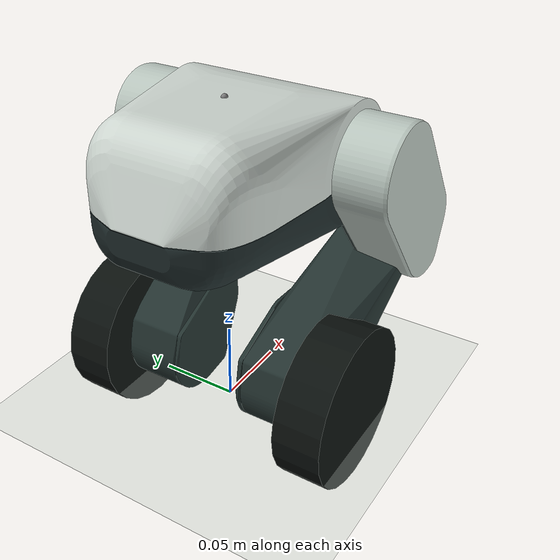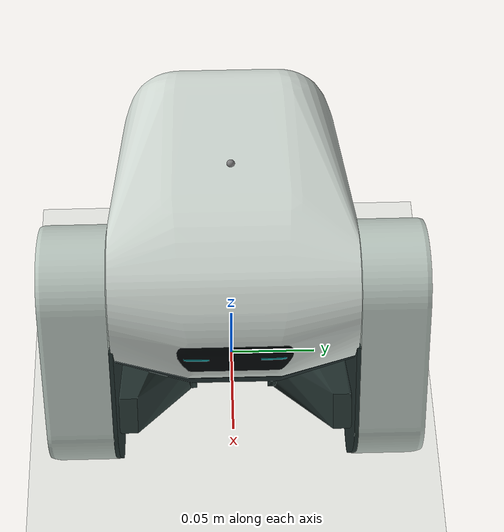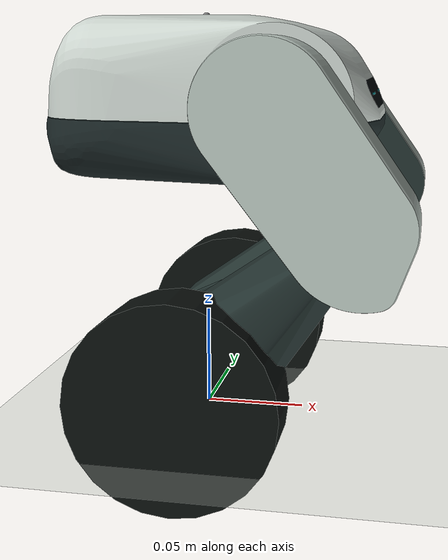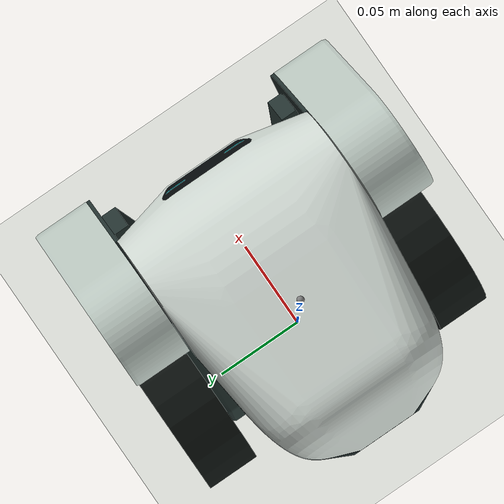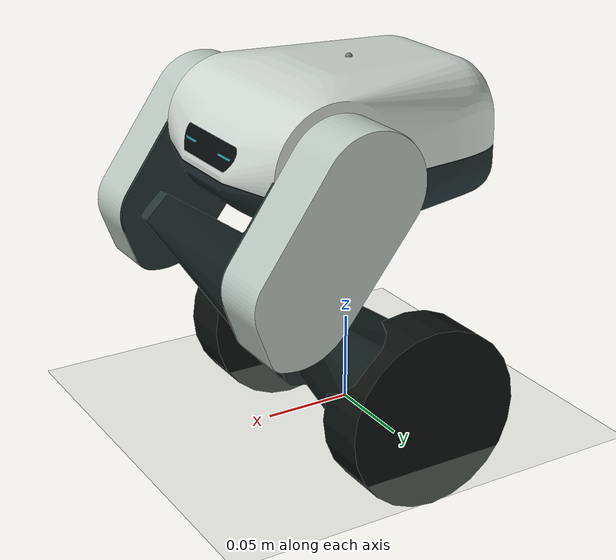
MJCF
<mujoco model="beni_internal_knees_v2806"><compiler angle="radian" autolimits="true" /><option timestep="0.00025" integrator="implicitfast" iterations="100" gravity="0 0 -9.81" /><visual><global offwidth="1280" offheight="960" /></visual><default><geom friction="0.8 0.005 0.0001" solref="0.003 1" solimp=".95 .99 .001" contype="2" conaffinity="1" /><joint damping=".002" frictionloss=".002" /></default><worldbody><geom name="ground" type="plane" size="4 4 .1" rgba=".78 .82 .78 1" contype="1" conaffinity="2" /><light pos="0 -1 2" dir="0 0 -1" /><body name="chassis" pos="0 0 .16"><freejoint name="root" /><site name="imu" pos="0 0 .04" size=".002" /><body name="left_upper" pos="0.04290204859622333 0.052 0.0" quat="0.9110387329540337 0.0 0.41232078174342474 0.0"><joint name="left_hip" type="hinge" axis="0 1 0" ref="0.85" range=".33 1.52" armature="0.0016799999999999999" /><site name="left_spring_upper" pos="0.021481877461693097 0.0295 0.0" size=".002" /><body name="left_lower" pos="0.0644818774616931 0.0 0.0" quat="0.7322835643236859 0.0 0.6809998395164262 0.0"><joint name="left_knee" type="hinge" axis="0 1 0" ref="1.4982542827942535" range=".42 2.39" /><site name="left_spring_lower" pos="0.025 0.0295 0.0" size=".002" /><site name="left_close_lower" pos="-0.0144367061504 0.017 0.00462678241615" size=".002" /><body name="left_wheel" pos="0.11911935079120996 0.023 0.0" quat="0.38634830440795476 0.0 -0.9223529626347488 0.0"><joint name="left_wheel" type="hinge" axis="0 1 0" damping=".0003" frictionloss=".001" armature="0.0001275" /><geom name="left_tire" type="cylinder" size=".05 .015" quat=".70710678 .70710678 0 0" condim="4" rgba=".045 .065 .055 1" /><inertial pos="-5.20540323111e-17 -0.00875423270895 -6.20280256568e-17" mass="0.35398557319780966" fullinertia="0.000222475894376 0.000323490525497 0.000222475894376 -2.66361823023e-19 5.13023629169e-19 -3.15547669306e-19" /></body><inertial pos="0.0728148891984 -0.00384272847487 0.000217999189759" mass="0.17493788265602236" fullinertia="7.14365863645e-05 0.000400888834382 0.000433997522655 7.65739907467e-05 3.30424209955e-06 -7.11190161464e-07" /><geom name="left_slim_lower_pod_collision" type="mesh" mesh="left_slim_lower_pod_collision_mesh" rgba="0.14 0.2 0.19 1" mass="0" contype="2" conaffinity="1" /><geom name="left_wheel_motor_mount_lid_collision" type="mesh" mesh="left_wheel_motor_mount_lid_collision_mesh" rgba="0.14 0.2 0.19 1" mass="0" contype="2" conaffinity="1" /></body><inertial pos="0.0145099956949 0.0122721672782 -0.000986332345462" mass="0.14305890995318365" fullinertia="8.00420153653e-05 0.000150609426752 0.000168103465971 -2.21404988817e-05 7.09775036861e-06 1.82200399338e-06" /><geom name="left_covered_thigh_collision" type="mesh" mesh="left_covered_thigh_collision_mesh" rgba="0.74 0.79 0.76 1" mass="0" contype="2" conaffinity="1" /><geom name="left_thigh_service_lid_collision" type="mesh" mesh="left_thigh_service_lid_collision_mesh" rgba="0.14 0.2 0.19 1" mass="0" contype="2" conaffinity="1" /></body><body name="left_tie" pos="0.061582048596223335 0.052 0.01255" quat="0.8856368218724082 0.0 0.4643785306662446 0.0"><joint name="left_tie" type="hinge" axis="0 1 0" ref="0.9658655234388" /><site name="left_close_tie" pos="0.06559 0.017 0" size=".002" /><inertial pos="0.032795 0.017 -3.49337897921e-19" mass="0.017363745970424258" fullinertia="1.27165523713e-07 7.30100947614e-06 7.22014727502e-06 1.82772055268e-21 2.47292450961e-22 1.93687732519e-23" /></body><body name="right_upper" pos="0.04290204859622333 -0.052 0.0" quat="0.9110387329540337 0.0 0.41232078174342474 0.0"><joint name="right_hip" type="hinge" axis="0 1 0" ref="0.85" range=".33 1.52" armature="0.0016799999999999999" /><site name="right_spring_upper" pos="0.021481877461693097 -0.0295 0.0" size=".002" /><body name="right_lower" pos="0.0644818774616931 0.0 0.0" quat="0.7322835643236859 0.0 0.6809998395164262 0.0"><joint name="right_knee" type="hinge" axis="0 1 0" ref="1.4982542827942535" range=".42 2.39" /><site name="right_spring_lower" pos="0.025 -0.0295 0.0" size=".002" /><site name="right_close_lower" pos="-0.0144367061504 -0.017 0.00462678241615" size=".002" /><body name="right_wheel" pos="0.11911935079120996 -0.023 0.0" quat="0.38634830440795476 0.0 -0.9223529626347488 0.0"><joint name="right_wheel" type="hinge" axis="0 1 0" damping=".0003" frictionloss=".001" armature="0.0001275" /><geom name="right_tire" type="cylinder" size=".05 .015" quat=".70710678 .70710678 0 0" condim="4" rgba=".045 .065 .055 1" /><inertial pos="-5.20540323111e-17 0.00875423270895 -6.20280256568e-17" mass="0.35398557319780966" fullinertia="0.000222475894376 0.000323490525497 0.000222475894376 2.71023535016e-19 5.13023629169e-19 3.16384850593e-19" /></body><inertial pos="0.0728148891984 0.00384272847487 0.000217999189759" mass="0.17493788265602236" fullinertia="7.14365863645e-05 0.000400888834382 0.000433997522655 -7.65739907467e-05 3.30424209955e-06 7.11190161464e-07" /><geom name="right_slim_lower_pod_collision" type="mesh" mesh="right_slim_lower_pod_collision_mesh" rgba="0.14 0.2 0.19 1" mass="0" contype="2" conaffinity="1" /><geom name="right_wheel_motor_mount_lid_collision" type="mesh" mesh="right_wheel_motor_mount_lid_collision_mesh" rgba="0.14 0.2 0.19 1" mass="0" contype="2" conaffinity="1" /></body><inertial pos="0.0145099956949 -0.0122721672782 -0.000986332345462" mass="0.14305890995318365" fullinertia="8.00420153653e-05 0.000150609426752 0.000168103465971 2.21404988817e-05 7.09775036861e-06 -1.82200399338e-06" /><geom name="right_covered_thigh_collision" type="mesh" mesh="right_covered_thigh_collision_mesh" rgba="0.74 0.79 0.76 1" mass="0" contype="2" conaffinity="1" /><geom name="right_thigh_service_lid_collision" type="mesh" mesh="right_thigh_service_lid_collision_mesh" rgba="0.14 0.2 0.19 1" mass="0" contype="2" conaffinity="1" /></body><body name="right_tie" pos="0.061582048596223335 -0.052 0.01255" quat="0.8856368218724082 0.0 0.4643785306662446 0.0"><joint name="right_tie" type="hinge" axis="0 1 0" ref="0.9658655234388" /><site name="right_close_tie" pos="0.06559 -0.017 0" size=".002" /><inertial pos="0.032795 -0.017 -3.87885528036e-19" mass="0.017363745970424258" fullinertia="1.27165523713e-07 7.30100947614e-06 7.22014727502e-06 1.82772055268e-21 2.28911499089e-22 -1.69145586426e-23" /></body><inertial pos="0.00461249688278 -1.20203335639e-09 0.00246550502092" mass="1.01223452413207" fullinertia="0.00153363379353 0.0018387792416 0.00248010355851 1.38388749249e-05 -8.06145890443e-05 -1.94460162224e-11" /><geom name="streamlined_upper_shell_collision" type="mesh" mesh="streamlined_upper_shell_collision_mesh" rgba="0.82 0.855 0.83 1" mass="0" contype="2" conaffinity="1" /><geom name="streamlined_lower_tray_collision" type="mesh" mesh="streamlined_lower_tray_collision_mesh" rgba="0.12 0.17 0.17 1" mass="0" contype="2" conaffinity="1" /><geom name="flush_visor_collision" type="mesh" mesh="flush_visor_collision_mesh" rgba="0.018 0.035 0.04 1" mass="0" contype="2" conaffinity="1" /><geom name="visor_light_0_collision" type="mesh" mesh="visor_light_0_collision_mesh" rgba="0.1 0.7 0.72 1" mass="0" contype="2" conaffinity="1" /><geom name="visor_light_1_collision" type="mesh" mesh="visor_light_1_collision_mesh" rgba="0.1 0.7 0.72 1" mass="0" contype="2" conaffinity="1" /></body></worldbody><equality><connect name="left_closure" site1="left_close_lower" site2="left_close_tie" solref=".001 1" solimp=".999 .9999 .0001" /><connect name="right_closure" site1="right_close_lower" site2="right_close_tie" solref=".001 1" solimp=".999 .9999 .0001" /></equality><tendon><spatial name="left_spring" stiffness="5500" springlength=".05 1" damping="0.0" width=".003" rgba=".9 .64 .2 1"><site site="left_spring_upper" /><site site="left_spring_lower" /></spatial><spatial name="right_spring" stiffness="5500" springlength=".05 1" damping="0.0" width=".003" rgba=".9 .64 .2 1"><site site="right_spring_upper" /><site site="right_spring_lower" /></spatial></tendon><actuator><motor name="left_wheel_drive" joint="left_wheel" ctrlrange="-0.771290339599 0.771290339599" /><motor name="right_wheel_drive" joint="right_wheel" ctrlrange="-0.771290339599 0.771290339599" /><motor name="left_hip_drive" joint="left_hip" ctrlrange="-8.81682313151 8.81682313151" /><motor name="right_hip_drive" joint="right_hip" ctrlrange="-8.81682313151 8.81682313151" /></actuator><sensor><gyro name="gyro" site="imu" /><accelerometer name="accelerometer" site="imu" /></sensor><asset><mesh name="left_slim_lower_pod_collision_mesh" vertex="-0.009 0.004 0.009 -0.009 -0.004 0.009 -0.009 -0.004 -0.009 -0.0082757 0.0065 -0.0035372 -0.0085595 0.0065 -0.0027812 -0.0087744 0.0065 -0.0020027 -0.0089185 0.0065 -0.0012081 -0.0089909 0.0065 -0.0004038 -0.009 0.004 -0.009 0.0656861 -0.028 -0.0020783 0.0655122 -0.028 -0.0018555 0.0652266 -0.028 -0.0013682 0.0651172 -0.028 -0.0011076 0.0649692 -0.028 -0.0005626 0.0649318 -0.028 -0.0002824 0.0649194 -0.028 0 0.0649318 -0.028 0.0002824 0.0649692 -0.028 0.0005626 0.0650311 -0.028 0.0008384 0.0651172 -0.028 0.0011076 0.0652266 -0.028 0.0013682 0.0653586 -0.028 0.0016182 0.0655122 -0.028 0.0018555 0.0656861 -0.028 0.0020783 0.0748492 -0.028 0.0122394 0.0759339 -0.028 0.0134009 0.0771128 -0.028 0.0144666 0.0783776 -0.028 0.015429 0.0797191 -0.028 0.0162811 0.0811278 -0.028 0.0170169 0.0825936 -0.028 0.0176311 -0.0089909 0.0065 0.0004038 -0.0089185 0.0065 0.0012081 -0.0087744 0.0065 0.0020027 -0.0085595 0.0065 0.0027812 -0.0082757 0.0065 0.0035372 0.0825936 -0.028 -0.0176311 0.0811278 -0.028 -0.0170169 0.0797191 -0.028 -0.0162811 0.0783776 -0.028 -0.015429 0.0771128 -0.028 -0.0144666 0.0759339 -0.028 -0.0134009 0.0748492 -0.028 -0.0122394 0.0653586 -0.028 -0.0016182 0.0650311 -0.028 -0.0008384 0.1201046 -0.028 0.0320445 0.1198288 -0.028 0.0321204 0.1195473 -0.028 0.0321713 0.1192624 -0.028 0.0321968 0.1189763 -0.028 0.0321968 0.1186914 -0.028 0.0321713 0.1184099 -0.028 0.0321204 0.1178661 -0.028 0.0319444 0.1344359 -0.028 0.0219919 0.1362991 -0.028 0.0205693 0.1396178 -0.028 0.0172642 0.141048 -0.028 0.015407 0.1433954 -0.028 0.0113539 0.1442947 -0.028 0.0091892 0.1458168 -0.028 0.0023419 0.1459194 -0.028 0 0.1458168 -0.028 -0.0023419 0.1455101 -0.028 -0.0046658 0.1442947 -0.028 -0.0091892 0.1423104 -0.028 -0.0134318 0.141048 -0.028 -0.015407 0.1380308 -0.028 -0.0189894 0.1203726 -0.028 -0.0319444 0.1201046 -0.028 -0.0320445 0.1198288 -0.028 -0.0321204 0.1195473 -0.028 -0.0321713 0.1192624 -0.028 -0.0321968 0.1189763 -0.028 -0.0321968 0.1186914 -0.028 -0.0321713 0.1184099 -0.028 -0.0321204 0.025 0.032 0.0055 0.0259821 0.032 0.0054116 0.0269326 0.032 0.0051493 0.0278209 0.032 0.0047215 0.0282328 0.032 0.0044496 0.0289754 0.032 0.0038008 0.0293001 0.032 0.0034292 0.0302308 0.032 0.0016996 0.0304502 0.032 0.0007383 0.0304945 0.032 0.0002468 0.0304945 0.032 -0.0002468 0.0304502 0.032 -0.0007383 0.0302308 0.032 -0.0016996 0.0289754 0.032 -0.0038008 0.0282328 0.032 -0.0044496 0.0278209 0.032 -0.0047215 0.0269326 0.032 -0.0051493 0.0264632 0.032 -0.0053018 0.025 0.032 -0.0055 0.024507 0.032 -0.0054779 0.0235368 0.032 -0.0053018 0.0230674 0.032 -0.0051493 0.0226136 0.032 -0.0049553 0.0217672 0.032 -0.0044496 0.0213813 0.032 -0.0041419 0.0210246 0.032 -0.0038008 0.0206999 0.032 -0.0034292 0.0204098 0.032 -0.0030299 0.0201567 0.032 -0.0026063 0.0199426 0.032 -0.0021616 0.0197692 0.032 -0.0016996 0.0196379 0.032 -0.0012239 0.0195055 0.032 0.0002468 0.0196379 0.032 0.0012239 0.0197692 0.032 0.0016996 0.0199426 0.032 0.0021616 0.0201567 0.032 0.0026063 0.0204098 0.032 0.0030299 0.0206999 0.032 0.0034292 0.0210246 0.032 0.0038008 0.0213813 0.032 0.0041419 0.0217672 0.032 0.0044496 0.0221791 0.032 0.0047215 0.0226136 0.032 0.0049553 0.0230674 0.032 0.0051493 0.0235368 0.032 0.0053018 0.0240179 0.032 0.0054116 0.024507 0.032 0.0054779 0.1208764 -0.028 0.0316745 0.1206305 -0.028 0.0318207 0.1203726 -0.028 0.0319444 0.1181341 -0.028 0.0320445 0.1185575 0.0055 0.0321503 0.1188373 0.0055 0.0321875 0.1194014 0.0055 0.0321875 0.1199567 0.0055 0.0320885 0.1202256 0.0055 0.0320027 0.120486 0.0055 0.0318935 0.1207357 0.0055 0.0317618 0.14259 -0.0268 0.0152686 0.1449168 -0.0268 0.0108855 0.1464333 -0.0268 0.0061604 0.1468717 -0.0268 0.0037157 0.1468717 -0.0268 -0.0037157 0.1464333 -0.0268 -0.0061604 0.1457799 -0.0268 -0.0085566 0.1411446 -0.0268 -0.0172884 0.1395259 -0.0268 -0.0191721 0.1377467 -0.0268 -0.0209051 0.1380308 -0.028 0.0189894 0.1423104 -0.028 0.0134318 0.1450014 -0.028 0.0069541 0.1455101 -0.028 0.0046658 0.1450014 -0.028 -0.0069541 0.1433954 -0.028 -0.0113539 0.1396178 -0.028 -0.0172642 0.1362991 -0.028 -0.0205693 0.1344359 -0.028 -0.0219919 0.1207357 0.0055 -0.0317618 0.120486 0.0055 -0.0318935 0.1199567 0.0055 -0.0320885 0.1196812 0.0055 -0.0321503 0.1191194 0.0055 -0.0322 0.1185575 0.0055 -0.0321503 0.1208764 -0.028 -0.0316745 0.1206305 -0.028 -0.0318207 0.1181341 -0.028 -0.0320445 0.1178661 -0.028 -0.0319444 0.025493 0.032 0.0054779 0.0264632 0.032 0.0053018 0.0273864 0.032 0.0049553 0.0286187 0.032 0.0041419 0.0295902 0.032 0.0030299 0.0298433 0.032 0.0026063 0.0300574 0.032 0.0021616 0.0303621 0.032 0.0012239 0.0303621 0.032 -0.0012239 0.0300574 0.032 -0.0021616 0.0298433 0.032 -0.0026063 0.0295902 0.032 -0.0030299 0.0293001 0.032 -0.0034292 0.0286187 0.032 -0.0041419 0.0273864 0.032 -0.0049553 0.0259821 0.032 -0.0054116 0.025493 0.032 -0.0054779 0.0240179 0.032 -0.0054116 0.0221791 0.032 -0.0047215 0.0195498 0.032 -0.0007383 0.0195055 0.032 -0.0002468 0.0195498 0.032 0.0007383 0.1360069 0.006 0.0223341 0.1396543 0.006 0.0190346 0.1412467 0.006 0.0171575 0.1426681 0.006 0.0151478 0.1439075 0.006 0.013021 0.1464454 0.006 0.0061064 0.1468761 0.006 0.0036828 0.1470923 0.006 0.0012308 0.1470923 0.006 -0.0012308 0.1468761 0.006 -0.0036828 0.1464454 0.006 -0.0061064 0.1449553 0.006 -0.0107936 0.1426681 0.006 -0.0151478 0.1412467 0.006 -0.0171575 0.1396543 0.006 -0.0190346 0.1379032 0.006 -0.0207646 0.1360069 0.006 -0.0223341 0.1339801 0.006 -0.023731 0.1191194 0.018 0.02 0.1226905 0.018 0.0196786 0.1244401 0.018 0.0192793 0.1261468 0.018 0.0187247 0.1308751 0.018 0.0161803 0.1322781 0.018 0.0150614 0.1335752 0.018 0.0138213 0.1367313 0.018 0.0094774 0.1389383 0.018 0.0026847 0.1390992 0.018 -0.0008973 0.1389383 0.018 -0.0026847 0.1375099 0.018 -0.0078605 0.1367313 0.018 -0.0094774 0.1358108 0.018 -0.0110179 0.1335752 0.018 -0.0138213 0.1308751 0.018 -0.0161803 0.1293773 0.018 -0.017169 0.127797 0.018 -0.0180194 0.1261468 0.018 -0.0187247 0.1244401 0.018 -0.0192793 0.1209121 0.018 -0.0199195 0.1191194 0.018 -0.02 0.1191194 0.0055 0.0322 0.1196812 0.0055 0.0321503 0.1202256 0.0055 -0.0320027 0.1194014 0.0055 -0.0321875 0.1188373 0.0055 -0.0321875 0.1339801 0.006 0.023731 0.1379032 0.006 0.0207646 0.1449553 0.006 0.0107936 0.1458035 0.006 0.0084828 0.1458035 0.006 -0.0084828 0.1439075 0.006 -0.013021 0.1337637 -0.0268 0.0238651 0.1358209 -0.0268 0.0224735 0.1377467 -0.0268 0.0209051 0.1395259 -0.0268 0.0191721 0.1411446 -0.0268 0.0172884 0.1438507 -0.0268 0.0131287 0.1457799 -0.0268 0.0085566 0.1470918 -0.0268 0.0012418 0.1470918 -0.0268 -0.0012418 0.1449168 -0.0268 -0.0108855 0.1438507 -0.0268 -0.0131287 0.14259 -0.0268 -0.0152686 0.1358209 -0.0268 -0.0224735 0.1337637 -0.0268 -0.0238651 0.1209121 0.018 0.0199195 0.127797 0.018 0.0180194 0.1293773 0.018 0.017169 0.134756 0.018 0.0124698 0.1358108 0.018 0.0110179 0.1375099 0.018 0.0078605 0.1381405 0.018 0.0061803 0.1386179 0.018 0.0044504 0.1390992 0.018 0.0008973 0.1386179 0.018 -0.0044504 0.1381405 0.018 -0.0061803 0.134756 0.018 -0.0124698 0.1322781 0.018 -0.0150614 0.1226905 0.018 -0.0196786" /><mesh name="left_wheel_motor_mount_lid_collision_mesh" vertex="0.0797191 -0.031 -0.0162811 0.0783776 -0.031 -0.015429 0.0771128 -0.031 -0.0144666 0.0759339 -0.031 -0.0134009 0.0748492 -0.031 -0.0122394 0.0656861 -0.031 0.0020783 0.0655122 -0.031 0.0018555 0.0653586 -0.031 0.0016182 0.0652266 -0.031 0.0013682 0.0650311 -0.031 0.0008384 0.0649318 -0.031 0.0002824 0.0649194 -0.031 -0 0.0649318 -0.031 -0.0002824 0.0649692 -0.031 -0.0005626 0.0651172 -0.031 -0.0011076 0.0653586 -0.031 -0.0016182 0.0655122 -0.031 -0.0018555 0.0759339 -0.031 0.0134009 0.0771128 -0.031 0.0144666 0.0783776 -0.031 0.015429 0.0797191 -0.031 0.0162811 0.0811278 -0.031 0.0170169 0.0825936 -0.031 0.0176311 0.1201046 -0.031 0.0320445 0.1198288 -0.031 0.0321204 0.1195473 -0.031 0.0321713 0.1192624 -0.031 0.0321968 0.1189763 -0.031 0.0321968 0.1380308 -0.031 0.0189894 0.141048 -0.031 0.015407 0.1442947 -0.031 0.0091892 0.1455101 -0.031 0.0046658 0.1459194 -0.031 0 0.1458168 -0.031 -0.0023419 0.1433954 -0.031 -0.0113539 0.1423104 -0.031 -0.0134318 0.141048 -0.031 -0.015407 0.1396178 -0.031 -0.0172642 0.1362991 -0.031 -0.0205693 0.1344359 -0.031 -0.0219919 0.1208764 -0.031 -0.0316745 0.1201046 -0.031 -0.0320445 0.1198288 -0.031 -0.0321204 0.1195473 -0.031 -0.0321713 0.1192624 -0.031 -0.0321968 0.1189763 -0.031 -0.0321968 0.1186914 -0.031 -0.0321713 0.1184099 -0.031 -0.0321204 0.1181341 -0.031 -0.0320445 0.1178661 -0.031 -0.0319444 0.0748492 -0.031 0.0122394 0.074747 -0.0298 0.0139081 0.0774252 -0.0298 0.0162249 0.08047 -0.0298 0.018033 0.0821005 -0.0298 0.0187279 0.0825936 -0.031 -0.0176311 0.0811278 -0.031 -0.0170169 0.0789075 -0.0298 -0.0171965 0.0774252 -0.0298 -0.0162249 0.074747 -0.0298 -0.0139081 0.0735722 -0.0298 -0.0125811 0.1358209 -0.0298 0.0224735 0.1377467 -0.0298 0.0209051 0.14259 -0.0298 0.0152686 0.1438507 -0.0298 0.0131287 0.1449168 -0.0298 0.0108855 0.1457799 -0.0298 0.0085566 0.1468717 -0.0298 0.0037157 0.1470918 -0.0298 0.0012418 0.1470918 -0.0298 -0.0012418 0.1464333 -0.0298 -0.0061604 0.1457799 -0.0298 -0.0085566 0.1438507 -0.0298 -0.0131287 0.1411446 -0.0298 -0.0172884 0.1395259 -0.0298 -0.0191721 0.1377467 -0.0298 -0.0209051 0.1358209 -0.0298 -0.0224735 0.1337637 -0.0298 -0.0238651 0.1344359 -0.031 0.0219919 0.1362991 -0.031 0.0205693 0.1396178 -0.031 0.0172642 0.1423104 -0.031 0.0134318 0.1433954 -0.031 0.0113539 0.1450014 -0.031 0.0069541 0.1458168 -0.031 0.0023419 0.1455101 -0.031 -0.0046658 0.1450014 -0.031 -0.0069541 0.1442947 -0.031 -0.0091892 0.1380308 -0.031 -0.0189894 0.1208764 -0.031 0.0316745 0.1206305 -0.031 0.0318207 0.1203726 -0.031 0.0319444 0.1186914 -0.031 0.0321713 0.1184099 -0.031 0.0321204 0.1181341 -0.031 0.0320445 0.1178661 -0.031 0.0319444 0.1207357 -0.0282 0.0317618 0.120486 -0.0282 0.0318935 0.1202256 -0.0282 0.0320027 0.1199567 -0.0282 0.0320885 0.1196812 -0.0282 0.0321503 0.1191194 -0.0282 0.0322 0.1188373 -0.0282 0.0321875 0.1185575 -0.0282 0.0321503 0.1180131 -0.0282 0.0320027 0.0821005 -0.0282 -0.0187279 0.08047 -0.0282 -0.018033 0.074747 -0.0282 -0.0139081 0.0655229 -0.0282 -0.0018704 0.0650332 -0.0282 -0.0008459 0.0649701 -0.0282 -0.0005677 0.0649321 -0.0282 -0.000285 0.0650332 -0.0282 0.0008459 0.0651208 -0.0282 0.0011174 0.0652322 -0.0282 0.0013801 0.0653666 -0.0282 0.0016317 0.0655229 -0.0282 0.0018704 0.074747 -0.0282 0.0139081 0.0760347 -0.0282 0.0151259 0.0774252 -0.0282 0.0162249 0.0789075 -0.0282 0.0171965 0.08047 -0.0282 0.018033 0.0821005 -0.0282 0.0187279 0.1194014 -0.0282 0.0321875 0.118282 -0.0282 0.0320885 0.1337637 -0.0282 0.0238651 0.1395259 -0.0282 0.0191721 0.1411446 -0.0282 0.0172884 0.1438507 -0.0282 0.0131287 0.1449168 -0.0282 0.0108855 0.1464333 -0.0282 0.0061604 0.1470918 -0.0282 0.0012418 0.1470918 -0.0282 -0.0012418 0.1457799 -0.0282 -0.0085566 0.1438507 -0.0282 -0.0131287 0.14259 -0.0282 -0.0152686 0.1358209 -0.0282 -0.0224735 0.1207357 -0.0282 -0.0317618 0.120486 -0.0282 -0.0318935 0.1196812 -0.0282 -0.0321503 0.1194014 -0.0282 -0.0321875 0.1191194 -0.0282 -0.0322 0.1188373 -0.0282 -0.0321875 0.1185575 -0.0282 -0.0321503 0.0735722 -0.0298 0.0125811 0.0760347 -0.0298 0.0151259 0.0789075 -0.0298 0.0171965 0.0735722 -0.0282 0.0125811 0.0653666 -0.0282 -0.0016317 0.0652322 -0.0282 -0.0013801 0.0651208 -0.0282 -0.0011174 0.0649194 -0.0282 -0 0.0649321 -0.0282 0.000285 0.0649701 -0.0282 0.0005677 0.0651172 -0.031 0.0011076 0.0649692 -0.031 0.0005626 0.0650311 -0.031 -0.0008384 0.0652266 -0.031 -0.0013682 0.0656861 -0.031 -0.0020783 0.1202256 -0.0282 -0.0320027 0.1199567 -0.0282 -0.0320885 0.118282 -0.0282 -0.0320885 0.1180131 -0.0282 -0.0320027 0.1206305 -0.031 -0.0318207 0.1203726 -0.031 -0.0319444 0.0821005 -0.0298 -0.0187279 0.08047 -0.0298 -0.018033 0.0760347 -0.0298 -0.0151259 0.0789075 -0.0282 -0.0171965 0.0774252 -0.0282 -0.0162249 0.0760347 -0.0282 -0.0151259 0.0735722 -0.0282 -0.0125811 0.1337637 -0.0298 0.0238651 0.1395259 -0.0298 0.0191721 0.1411446 -0.0298 0.0172884 0.1464333 -0.0298 0.0061604 0.1468717 -0.0298 -0.0037157 0.1449168 -0.0298 -0.0108855 0.14259 -0.0298 -0.0152686 0.1358209 -0.0282 0.0224735 0.1377467 -0.0282 0.0209051 0.14259 -0.0282 0.0152686 0.1457799 -0.0282 0.0085566 0.1468717 -0.0282 0.0037157 0.1468717 -0.0282 -0.0037157 0.1464333 -0.0282 -0.0061604 0.1449168 -0.0282 -0.0108855 0.1411446 -0.0282 -0.0172884 0.1395259 -0.0282 -0.0191721 0.1377467 -0.0282 -0.0209051 0.1337637 -0.0282 -0.0238651 0.1191194 -0.0195 0.01 0.1226331 -0.0195 0.0093623 0.1234582 -0.0195 0.0090097 0.1242483 -0.0195 0.0085845 0.1256987 -0.0195 0.0075307 0.1274651 -0.0195 0.005509 0.1279253 -0.0195 0.0047387 0.1286299 -0.0195 0.0030902 0.1290288 -0.0195 0.0013423 0.1291093 -0.0195 -0.0004486 0.1290288 -0.0195 -0.0013423 0.1279253 -0.0195 -0.0047387 0.1269377 -0.0195 -0.0062349 0.1242483 -0.0195 -0.0085845 0.1217797 -0.0195 -0.0096396 0.1209049 -0.0195 -0.0098393 0.1200157 -0.0195 -0.0099597 0.118223 -0.0195 -0.0099597 0.1173338 -0.0195 -0.0098393 0.116459 -0.0195 -0.0096396 0.1156056 -0.0195 -0.0093623 0.1139904 -0.0195 -0.0085845 0.1132415 -0.0195 -0.0080902 0.11254 -0.0195 -0.0075307 0.111301 -0.0195 -0.0062349 0.1099241 -0.0195 -0.0039303 0.1093701 -0.0195 -0.0022252 0.1092099 -0.0195 -0.0013423 0.1091294 -0.0195 0.0004486 0.1092099 -0.0195 0.0013423 0.1093701 -0.0195 0.0022252 0.1096088 -0.0195 0.0030902 0.111301 -0.0195 0.0062349 0.1139904 -0.0195 0.0085845 0.1147805 -0.0195 0.0090097 0.1156056 -0.0195 0.0093623 0.116459 -0.0195 0.0096396 0.1173338 -0.0195 0.0098393 0.118223 -0.0195 0.0099597 0.1200157 -0.0195 0.0099597 0.1209049 -0.0195 0.0098393 0.1217797 -0.0195 0.0096396 0.1249972 -0.0195 0.0080902 0.1263473 -0.0195 0.0069106 0.1269377 -0.0195 0.0062349 0.1283146 -0.0195 0.0039303 0.1288686 -0.0195 0.0022252 0.1291093 -0.0195 0.0004486 0.1288686 -0.0195 -0.0022252 0.1286299 -0.0195 -0.0030902 0.1283146 -0.0195 -0.0039303 0.1274651 -0.0195 -0.005509 0.1263473 -0.0195 -0.0069106 0.1256987 -0.0195 -0.0075307 0.1249972 -0.0195 -0.0080902 0.1234582 -0.0195 -0.0090097 0.1226331 -0.0195 -0.0093623 0.1191194 -0.0195 -0.01 0.1147805 -0.0195 -0.0090097 0.1118914 -0.0195 -0.0069106 0.1107736 -0.0195 -0.005509 0.1103134 -0.0195 -0.0047387 0.1096088 -0.0195 -0.0030902 0.1091294 -0.0195 -0.0004486 0.1099241 -0.0195 0.0039303 0.1103134 -0.0195 0.0047387 0.1107736 -0.0195 0.005509 0.1118914 -0.0195 0.0069106 0.11254 -0.0195 0.0075307 0.1132415 -0.0195 0.0080902" /><mesh name="right_slim_lower_pod_collision_mesh" vertex="-0.009 -0.004 0.009 -0.009 0.004 0.009 -0.009 0.004 -0.009 -0.0082757 -0.0065 -0.0035372 -0.0085595 -0.0065 -0.0027812 -0.0087744 -0.0065 -0.0020027 -0.0089185 -0.0065 -0.0012081 -0.0089909 -0.0065 -0.0004038 -0.009 -0.004 -0.009 0.0656861 0.028 0.0020783 0.0655122 0.028 0.0018555 0.0653586 0.028 0.0016182 0.0652266 0.028 0.0013682 0.0651172 0.028 0.0011076 0.0650311 0.028 0.0008384 0.0649692 0.028 0.0005626 0.0649318 0.028 0.0002824 0.0649194 0.028 0 0.0650311 0.028 -0.0008384 0.0651172 0.028 -0.0011076 0.0652266 0.028 -0.0013682 0.0653586 0.028 -0.0016182 0.0655122 0.028 -0.0018555 0.0656861 0.028 -0.0020783 0.0748492 0.028 0.0122394 0.0759339 0.028 0.0134009 0.0771128 0.028 0.0144666 0.0783776 0.028 0.015429 0.0797191 0.028 0.0162811 0.0811278 0.028 0.0170169 0.0825936 0.028 0.0176311 -0.0089909 -0.0065 0.0004038 -0.0089185 -0.0065 0.0012081 -0.0087744 -0.0065 0.0020027 -0.0085595 -0.0065 0.0027812 -0.0082757 -0.0065 0.0035372 0.0825936 0.028 -0.0176311 0.0811278 0.028 -0.0170169 0.0797191 0.028 -0.0162811 0.0783776 0.028 -0.015429 0.0771128 0.028 -0.0144666 0.0759339 0.028 -0.0134009 0.0748492 0.028 -0.0122394 0.0649318 0.028 -0.0002824 0.0649692 0.028 -0.0005626 0.1178661 0.028 0.0319444 0.1184099 0.028 0.0321204 0.1186914 0.028 0.0321713 0.1189763 0.028 0.0321968 0.1192624 0.028 0.0321968 0.1195473 0.028 0.0321713 0.1198288 0.028 0.0321204 0.1201046 0.028 0.0320445 0.1206305 0.028 0.0318207 0.1344359 0.028 0.0219919 0.1362991 0.028 0.0205693 0.1396178 0.028 0.0172642 0.141048 0.028 0.015407 0.1433954 0.028 0.0113539 0.1442947 0.028 0.0091892 0.1458168 0.028 0.0023419 0.1459194 0.028 0 0.1458168 0.028 -0.0023419 0.1455101 0.028 -0.0046658 0.1442947 0.028 -0.0091892 0.1423104 0.028 -0.0134318 0.141048 0.028 -0.015407 0.1380308 0.028 -0.0189894 0.1203726 0.028 -0.0319444 0.1201046 0.028 -0.0320445 0.1198288 0.028 -0.0321204 0.1195473 0.028 -0.0321713 0.1192624 0.028 -0.0321968 0.1189763 0.028 -0.0321968 0.1186914 0.028 -0.0321713 0.1184099 0.028 -0.0321204 0.025 -0.032 0.0055 0.0259821 -0.032 0.0054116 0.0269326 -0.032 0.0051493 0.0278209 -0.032 0.0047215 0.0282328 -0.032 0.0044496 0.0289754 -0.032 0.0038008 0.0293001 -0.032 0.0034292 0.0302308 -0.032 0.0016996 0.0304502 -0.032 0.0007383 0.0304945 -0.032 0.0002468 0.0304945 -0.032 -0.0002468 0.0304502 -0.032 -0.0007383 0.0302308 -0.032 -0.0016996 0.0289754 -0.032 -0.0038008 0.0282328 -0.032 -0.0044496 0.0278209 -0.032 -0.0047215 0.0269326 -0.032 -0.0051493 0.0264632 -0.032 -0.0053018 0.025 -0.032 -0.0055 0.024507 -0.032 -0.0054779 0.0235368 -0.032 -0.0053018 0.0230674 -0.032 -0.0051493 0.0226136 -0.032 -0.0049553 0.0217672 -0.032 -0.0044496 0.0213813 -0.032 -0.0041419 0.0210246 -0.032 -0.0038008 0.0206999 -0.032 -0.0034292 0.0204098 -0.032 -0.0030299 0.0201567 -0.032 -0.0026063 0.0199426 -0.032 -0.0021616 0.0197692 -0.032 -0.0016996 0.0196379 -0.032 -0.0012239 0.0195055 -0.032 0.0002468 0.0196379 -0.032 0.0012239 0.0197692 -0.032 0.0016996 0.0199426 -0.032 0.0021616 0.0201567 -0.032 0.0026063 0.0204098 -0.032 0.0030299 0.0206999 -0.032 0.0034292 0.0210246 -0.032 0.0038008 0.0213813 -0.032 0.0041419 0.0217672 -0.032 0.0044496 0.0221791 -0.032 0.0047215 0.0226136 -0.032 0.0049553 0.0230674 -0.032 0.0051493 0.0235368 -0.032 0.0053018 0.0240179 -0.032 0.0054116 0.024507 -0.032 0.0054779 0.1181341 0.028 0.0320445 0.1203726 0.028 0.0319444 0.1208764 0.028 0.0316745 0.1207357 -0.0055 0.0317618 0.120486 -0.0055 0.0318935 0.1202256 -0.0055 0.0320027 0.1185575 -0.0055 0.0321503 0.14259 0.0268 0.0152686 0.1449168 0.0268 0.0108855 0.1464333 0.0268 0.0061604 0.1468717 0.0268 0.0037157 0.1468717 0.0268 -0.0037157 0.1464333 0.0268 -0.0061604 0.1457799 0.0268 -0.0085566 0.1411446 0.0268 -0.0172884 0.1395259 0.0268 -0.0191721 0.1377467 0.0268 -0.0209051 0.1380308 0.028 0.0189894 0.1423104 0.028 0.0134318 0.1450014 0.028 0.0069541 0.1455101 0.028 0.0046658 0.1450014 0.028 -0.0069541 0.1433954 0.028 -0.0113539 0.1396178 0.028 -0.0172642 0.1362991 0.028 -0.0205693 0.1344359 0.028 -0.0219919 0.1207357 -0.0055 -0.0317618 0.120486 -0.0055 -0.0318935 0.1199567 -0.0055 -0.0320885 0.1196812 -0.0055 -0.0321503 0.1191194 -0.0055 -0.0322 0.1185575 -0.0055 -0.0321503 0.1208764 0.028 -0.0316745 0.1206305 0.028 -0.0318207 0.1181341 0.028 -0.0320445 0.1178661 0.028 -0.0319444 0.025493 -0.032 0.0054779 0.0264632 -0.032 0.0053018 0.0273864 -0.032 0.0049553 0.0286187 -0.032 0.0041419 0.0295902 -0.032 0.0030299 0.0298433 -0.032 0.0026063 0.0300574 -0.032 0.0021616 0.0303621 -0.032 0.0012239 0.0303621 -0.032 -0.0012239 0.0300574 -0.032 -0.0021616 0.0298433 -0.032 -0.0026063 0.0295902 -0.032 -0.0030299 0.0293001 -0.032 -0.0034292 0.0286187 -0.032 -0.0041419 0.0273864 -0.032 -0.0049553 0.0259821 -0.032 -0.0054116 0.025493 -0.032 -0.0054779 0.0240179 -0.032 -0.0054116 0.0221791 -0.032 -0.0047215 0.0195498 -0.032 -0.0007383 0.0195055 -0.032 -0.0002468 0.0195498 -0.032 0.0007383 0.1360069 -0.006 0.0223341 0.1396543 -0.006 0.0190346 0.1412467 -0.006 0.0171575 0.1426681 -0.006 0.0151478 0.1439075 -0.006 0.013021 0.1464454 -0.006 0.0061064 0.1468761 -0.006 0.0036828 0.1470923 -0.006 0.0012308 0.1470923 -0.006 -0.0012308 0.1468761 -0.006 -0.0036828 0.1464454 -0.006 -0.0061064 0.1449553 -0.006 -0.0107936 0.1426681 -0.006 -0.0151478 0.1412467 -0.006 -0.0171575 0.1396543 -0.006 -0.0190346 0.1379032 -0.006 -0.0207646 0.1360069 -0.006 -0.0223341 0.1339801 -0.006 -0.023731 0.1191194 -0.018 0.02 0.1226905 -0.018 0.0196786 0.1244401 -0.018 0.0192793 0.1261468 -0.018 0.0187247 0.1308751 -0.018 0.0161803 0.1322781 -0.018 0.0150614 0.1335752 -0.018 0.0138213 0.1367313 -0.018 0.0094774 0.1389383 -0.018 0.0026847 0.1390992 -0.018 -0.0008973 0.1389383 -0.018 -0.0026847 0.1375099 -0.018 -0.0078605 0.1367313 -0.018 -0.0094774 0.1358108 -0.018 -0.0110179 0.1335752 -0.018 -0.0138213 0.1308751 -0.018 -0.0161803 0.1293773 -0.018 -0.017169 0.127797 -0.018 -0.0180194 0.1261468 -0.018 -0.0187247 0.1244401 -0.018 -0.0192793 0.1209121 -0.018 -0.0199195 0.1191194 -0.018 -0.02 0.1199567 -0.0055 0.0320885 0.1196812 -0.0055 0.0321503 0.1194014 -0.0055 0.0321875 0.1191194 -0.0055 0.0322 0.1188373 -0.0055 0.0321875 0.1202256 -0.0055 -0.0320027 0.1194014 -0.0055 -0.0321875 0.1188373 -0.0055 -0.0321875 0.1339801 -0.006 0.023731 0.1379032 -0.006 0.0207646 0.1449553 -0.006 0.0107936 0.1458035 -0.006 0.0084828 0.1458035 -0.006 -0.0084828 0.1439075 -0.006 -0.013021 0.1337637 0.0268 0.0238651 0.1358209 0.0268 0.0224735 0.1377467 0.0268 0.0209051 0.1395259 0.0268 0.0191721 0.1411446 0.0268 0.0172884 0.1438507 0.0268 0.0131287 0.1457799 0.0268 0.0085566 0.1470918 0.0268 0.0012418 0.1470918 0.0268 -0.0012418 0.1449168 0.0268 -0.0108855 0.1438507 0.0268 -0.0131287 0.14259 0.0268 -0.0152686 0.1358209 0.0268 -0.0224735 0.1337637 0.0268 -0.0238651 0.1209121 -0.018 0.0199195 0.127797 -0.018 0.0180194 0.1293773 -0.018 0.017169 0.134756 -0.018 0.0124698 0.1358108 -0.018 0.0110179 0.1375099 -0.018 0.0078605 0.1381405 -0.018 0.0061803 0.1386179 -0.018 0.0044504 0.1390992 -0.018 0.0008973 0.1386179 -0.018 -0.0044504 0.1381405 -0.018 -0.0061803 0.134756 -0.018 -0.0124698 0.1322781 -0.018 -0.0150614 0.1226905 -0.018 -0.0196786" /><mesh name="right_wheel_motor_mount_lid_collision_mesh" vertex="0.0797191 0.031 -0.0162811 0.0783776 0.031 -0.015429 0.0771128 0.031 -0.0144666 0.0759339 0.031 -0.0134009 0.0748492 0.031 -0.0122394 0.0656861 0.031 -0.0020783 0.0655122 0.031 -0.0018555 0.0653586 0.031 -0.0016182 0.0652266 0.031 -0.0013682 0.0651172 0.031 -0.0011076 0.0649692 0.031 -0.0005626 0.0649318 0.031 -0.0002824 0.0649194 0.031 0 0.0652266 0.031 0.0013682 0.0653586 0.031 0.0016182 0.0655122 0.031 0.0018555 0.0656861 0.031 0.0020783 0.0759339 0.031 0.0134009 0.0771128 0.031 0.0144666 0.0783776 0.031 0.015429 0.0797191 0.031 0.0162811 0.0811278 0.031 0.0170169 0.0825936 0.031 0.0176311 0.1178661 0.031 0.0319444 0.1184099 0.031 0.0321204 0.1189763 0.031 0.0321968 0.1192624 0.031 0.0321968 0.1195473 0.031 0.0321713 0.1198288 0.031 0.0321204 0.1201046 0.031 0.0320445 0.1380308 0.031 0.0189894 0.141048 0.031 0.015407 0.1442947 0.031 0.0091892 0.1455101 0.031 0.0046658 0.1459194 0.031 0 0.1458168 0.031 -0.0023419 0.1433954 0.031 -0.0113539 0.1423104 0.031 -0.0134318 0.141048 0.031 -0.015407 0.1396178 0.031 -0.0172642 0.1362991 0.031 -0.0205693 0.1344359 0.031 -0.0219919 0.1208764 0.031 -0.0316745 0.1201046 0.031 -0.0320445 0.1198288 0.031 -0.0321204 0.1195473 0.031 -0.0321713 0.1192624 0.031 -0.0321968 0.1189763 0.031 -0.0321968 0.1186914 0.031 -0.0321713 0.1184099 0.031 -0.0321204 0.1181341 0.031 -0.0320445 0.1178661 0.031 -0.0319444 0.0748492 0.031 0.0122394 0.074747 0.0298 0.0139081 0.0774252 0.0298 0.0162249 0.08047 0.0298 0.018033 0.0821005 0.0298 0.0187279 0.0825936 0.031 -0.0176311 0.0811278 0.031 -0.0170169 0.0789075 0.0298 -0.0171965 0.0774252 0.0298 -0.0162249 0.074747 0.0298 -0.0139081 0.0735722 0.0298 -0.0125811 0.1358209 0.0298 0.0224735 0.1377467 0.0298 0.0209051 0.14259 0.0298 0.0152686 0.1438507 0.0298 0.0131287 0.1449168 0.0298 0.0108855 0.1457799 0.0298 0.0085566 0.1468717 0.0298 0.0037157 0.1470918 0.0298 0.0012418 0.1470918 0.0298 -0.0012418 0.1464333 0.0298 -0.0061604 0.1457799 0.0298 -0.0085566 0.1438507 0.0298 -0.0131287 0.1411446 0.0298 -0.0172884 0.1395259 0.0298 -0.0191721 0.1377467 0.0298 -0.0209051 0.1358209 0.0298 -0.0224735 0.1337637 0.0298 -0.0238651 0.1344359 0.031 0.0219919 0.1362991 0.031 0.0205693 0.1396178 0.031 0.0172642 0.1423104 0.031 0.0134318 0.1433954 0.031 0.0113539 0.1450014 0.031 0.0069541 0.1458168 0.031 0.0023419 0.1455101 0.031 -0.0046658 0.1450014 0.031 -0.0069541 0.1442947 0.031 -0.0091892 0.1380308 0.031 -0.0189894 0.1181341 0.031 0.0320445 0.1186914 0.031 0.0321713 0.1203726 0.031 0.0319444 0.1206305 0.031 0.0318207 0.1208764 0.031 0.0316745 0.1180131 0.0282 0.0320027 0.1185575 0.0282 0.0321503 0.1188373 0.0282 0.0321875 0.1191194 0.0282 0.0322 0.1196812 0.0282 0.0321503 0.1199567 0.0282 0.0320885 0.1202256 0.0282 0.0320027 0.120486 0.0282 0.0318935 0.1207357 0.0282 0.0317618 0.0821005 0.0282 -0.0187279 0.08047 0.0282 -0.018033 0.074747 0.0282 -0.0139081 0.0655229 0.0282 0.0018704 0.0653666 0.0282 0.0016317 0.0652322 0.0282 0.0013801 0.0649701 0.0282 -0.0005677 0.0655229 0.0282 -0.0018704 0.074747 0.0282 0.0139081 0.0760347 0.0282 0.0151259 0.0774252 0.0282 0.0162249 0.0789075 0.0282 0.0171965 0.08047 0.0282 0.018033 0.0821005 0.0282 0.0187279 0.118282 0.0282 0.0320885 0.1194014 0.0282 0.0321875 0.1337637 0.0282 0.0238651 0.1395259 0.0282 0.0191721 0.1411446 0.0282 0.0172884 0.1438507 0.0282 0.0131287 0.1449168 0.0282 0.0108855 0.1464333 0.0282 0.0061604 0.1470918 0.0282 0.0012418 0.1470918 0.0282 -0.0012418 0.1457799 0.0282 -0.0085566 0.1438507 0.0282 -0.0131287 0.14259 0.0282 -0.0152686 0.1358209 0.0282 -0.0224735 0.1207357 0.0282 -0.0317618 0.120486 0.0282 -0.0318935 0.1196812 0.0282 -0.0321503 0.1194014 0.0282 -0.0321875 0.1191194 0.0282 -0.0322 0.1188373 0.0282 -0.0321875 0.1185575 0.0282 -0.0321503 0.0735722 0.0298 0.0125811 0.0760347 0.0298 0.0151259 0.0789075 0.0298 0.0171965 0.0735722 0.0282 0.0125811 0.0651208 0.0282 0.0011174 0.0650332 0.0282 0.0008459 0.0649701 0.0282 0.0005677 0.0649321 0.0282 0.000285 0.0649194 0.0282 0 0.0649321 0.0282 -0.000285 0.0650332 0.0282 -0.0008459 0.0651208 0.0282 -0.0011174 0.0652322 0.0282 -0.0013801 0.0653666 0.0282 -0.0016317 0.0650311 0.031 -0.0008384 0.0649318 0.031 0.0002824 0.0649692 0.031 0.0005626 0.0650311 0.031 0.0008384 0.0651172 0.031 0.0011076 0.1202256 0.0282 -0.0320027 0.1199567 0.0282 -0.0320885 0.118282 0.0282 -0.0320885 0.1180131 0.0282 -0.0320027 0.1206305 0.031 -0.0318207 0.1203726 0.031 -0.0319444 0.0821005 0.0298 -0.0187279 0.08047 0.0298 -0.018033 0.0760347 0.0298 -0.0151259 0.0789075 0.0282 -0.0171965 0.0774252 0.0282 -0.0162249 0.0760347 0.0282 -0.0151259 0.0735722 0.0282 -0.0125811 0.1337637 0.0298 0.0238651 0.1395259 0.0298 0.0191721 0.1411446 0.0298 0.0172884 0.1464333 0.0298 0.0061604 0.1468717 0.0298 -0.0037157 0.1449168 0.0298 -0.0108855 0.14259 0.0298 -0.0152686 0.1358209 0.0282 0.0224735 0.1377467 0.0282 0.0209051 0.14259 0.0282 0.0152686 0.1457799 0.0282 0.0085566 0.1468717 0.0282 0.0037157 0.1468717 0.0282 -0.0037157 0.1464333 0.0282 -0.0061604 0.1449168 0.0282 -0.0108855 0.1411446 0.0282 -0.0172884 0.1395259 0.0282 -0.0191721 0.1377467 0.0282 -0.0209051 0.1337637 0.0282 -0.0238651 0.1191194 0.0195 0.01 0.1226331 0.0195 0.0093623 0.1234582 0.0195 0.0090097 0.1242483 0.0195 0.0085845 0.1256987 0.0195 0.0075307 0.1274651 0.0195 0.005509 0.1279253 0.0195 0.0047387 0.1286299 0.0195 0.0030902 0.1290288 0.0195 0.0013423 0.1291093 0.0195 -0.0004486 0.1290288 0.0195 -0.0013423 0.1279253 0.0195 -0.0047387 0.1269377 0.0195 -0.0062349 0.1242483 0.0195 -0.0085845 0.1217797 0.0195 -0.0096396 0.1209049 0.0195 -0.0098393 0.1200157 0.0195 -0.0099597 0.118223 0.0195 -0.0099597 0.1173338 0.0195 -0.0098393 0.116459 0.0195 -0.0096396 0.1156056 0.0195 -0.0093623 0.1139904 0.0195 -0.0085845 0.1132415 0.0195 -0.0080902 0.11254 0.0195 -0.0075307 0.111301 0.0195 -0.0062349 0.1099241 0.0195 -0.0039303 0.1093701 0.0195 -0.0022252 0.1092099 0.0195 -0.0013423 0.1091294 0.0195 0.0004486 0.1092099 0.0195 0.0013423 0.1093701 0.0195 0.0022252 0.1096088 0.0195 0.0030902 0.111301 0.0195 0.0062349 0.1139904 0.0195 0.0085845 0.1147805 0.0195 0.0090097 0.1156056 0.0195 0.0093623 0.116459 0.0195 0.0096396 0.1173338 0.0195 0.0098393 0.118223 0.0195 0.0099597 0.1200157 0.0195 0.0099597 0.1209049 0.0195 0.0098393 0.1217797 0.0195 0.0096396 0.1249972 0.0195 0.0080902 0.1263473 0.0195 0.0069106 0.1269377 0.0195 0.0062349 0.1283146 0.0195 0.0039303 0.1288686 0.0195 0.0022252 0.1291093 0.0195 0.0004486 0.1288686 0.0195 -0.0022252 0.1286299 0.0195 -0.0030902 0.1283146 0.0195 -0.0039303 0.1274651 0.0195 -0.005509 0.1263473 0.0195 -0.0069106 0.1256987 0.0195 -0.0075307 0.1249972 0.0195 -0.0080902 0.1234582 0.0195 -0.0090097 0.1226331 0.0195 -0.0093623 0.1191194 0.0195 -0.01 0.1147805 0.0195 -0.0090097 0.1118914 0.0195 -0.0069106 0.1107736 0.0195 -0.005509 0.1103134 0.0195 -0.0047387 0.1096088 0.0195 -0.0030902 0.1091294 0.0195 -0.0004486 0.1099241 0.0195 0.0039303 0.1103134 0.0195 0.0047387 0.1107736 0.0195 0.005509 0.1118914 0.0195 0.0069106 0.11254 0.0195 0.0075307 0.1132415 0.0195 0.0080902" /><mesh name="streamlined_upper_shell_collision_mesh" vertex="-0.078 -0.013 -0.007 -0.078 -0.0135626 -0.0070226 -0.078 -0.0146733 -0.0072029 -0.078 -0.0157408 -0.0075589 -0.078 -0.0162496 -0.0078 -0.078 0.0152142 -0.0073594 -0.078 0.0135626 -0.0070226 -0.0656977 -0.0226981 0.0263435 -0.0642127 -0.0232804 0.0289881 -0.0627656 -0.023747 0.0311018 -0.0613761 -0.0241234 0.0327872 -0.0600577 -0.0244298 0.0341307 -0.0586782 -0.0247081 0.0353147 -0.057241 -0.0249608 0.0363452 -0.0557496 -0.0251907 0.0372297 -0.0542081 -0.0254005 0.0379767 -0.0509912 -0.0257696 0.0390968 -0.0453128 -0.0262782 0.040049 -0.0426625 -0.0264792 0.0401915 -0.0390681 -0.0267314 0.0401863 0.0169234 -0.027888 0.0400563 0.0267003 -0.0272403 0.0398938 0.073989 -0.0235737 0.0205201 0.0800923 -0.0216788 0.0126805 -0.078 -0.0141216 -0.0070904 -0.078 -0.0152142 -0.0073594 -0.06809 -0.0387792 0.003369 -0.0668682 -0.0401992 0.005775 -0.0645615 -0.0423729 0.0091958 -0.0633914 -0.0432908 0.0105021 -0.0586096 -0.0462217 0.0138676 -0.055916 -0.047481 0.0148248 -0.053051 -0.0486139 0.0153704 -0.0500404 -0.0496287 0.0155711 -0.0479656 -0.0502436 0.0155484 -0.0423239 -0.0516419 0.0150615 -0.0297676 -0.0537244 0.0132275 0.0223947 -0.0325667 0.0395728 0.0181235 -0.0328702 0.0395808 0.0270674 -0.0320994 0.0394008 -0.0482843 -0.0394317 0.0356173 -0.0502799 -0.0349157 0.0374733 -0.0518738 -0.0386506 0.0349052 -0.0445524 -0.0358261 0.038218 -0.0483166 -0.0460793 0.0289589 -0.0518738 -0.0421896 0.0320009 -0.0518738 -0.0450939 0.0284619 -0.050343 -0.0477297 0.0246337 -0.0446191 -0.0492297 0.0248015 -0.0415874 -0.0362166 0.0382891 -0.0424865 -0.0473739 0.0290344 -0.0416553 -0.0498644 0.024633 -0.0403285 -0.0501227 0.0245221 -0.0483005 -0.0430837 0.0326154 -0.0454184 -0.0437001 0.0328203 -0.0327524 -0.0528305 0.0187677 -0.0449861 -0.0400393 0.0359083 -0.0450193 -0.0468532 0.0290872 -0.0403285 -0.0316027 0.0397211 -0.0686317 -0.0243944 0.018801 -0.0655234 -0.0264329 0.0263223 -0.0655234 -0.0299522 0.0252548 -0.0686317 -0.0275816 0.0178342 -0.0655234 -0.0331956 0.0235211 -0.0686317 -0.030519 0.0162641 -0.0616485 -0.0280411 0.0320875 -0.0686317 -0.0367767 0.0086391 -0.0686317 -0.0352066 0.0115765 -0.0655234 -0.0360385 0.021188 -0.0686317 -0.0330937 0.0141511 -0.0616485 -0.0318747 0.0309246 -0.0686317 -0.0377435 0.0054519 -0.0655234 -0.0383716 0.0183451 -0.0616485 -0.0354077 0.0290361 -0.0570585 -0.0292791 0.0360405 -0.0655234 -0.0401053 0.0151017 -0.0616485 -0.0385044 0.0264947 -0.0570585 -0.0334029 0.0347895 -0.0655234 -0.0411729 0.0115823 -0.0616485 -0.0410458 0.023398 -0.0570585 -0.0372034 0.0327581 -0.0518738 -0.0302321 0.0383923 -0.0616485 -0.0429343 0.019865 -0.0570585 -0.0405346 0.0300243 -0.0518738 -0.0346131 0.0370633 -0.0616485 -0.0440972 0.0160314 -0.0570585 -0.0432684 0.0266931 -0.0570585 -0.0452998 0.0228927 -0.0570585 -0.0465507 0.0187689 -0.0518738 -0.047252 0.0244244 -0.0518738 -0.048581 0.0200434 -0.0403285 -0.0515688 0.019755 -0.0497768 -0.0305376 0.0389366 -0.0486526 -0.030688 0.0391569 -0.0428386 -0.0313557 0.0397049 -0.0487811 -0.0495477 0.0202575 -0.0429734 -0.0510174 0.0200255 -0.0388378 -0.0518521 0.0195768 -0.078 0.013 -0.007 -0.0656977 0.0226981 0.0263435 -0.0642127 0.0232804 0.0289881 -0.0613761 0.0241234 0.0327872 -0.0600577 0.0244298 0.0341307 -0.057241 0.0249608 0.0363452 -0.0557496 0.0251907 0.0372297 -0.0542081 0.0254005 0.0379767 -0.0509912 0.0257696 0.0390968 -0.0390681 0.0267314 0.0401863 0.0169234 0.027888 0.0400563 0.0267003 0.0272403 0.0398938 0.0415232 0.0263165 0.0377719 0.0711017 0.0241676 0.023325 0.073989 0.0235737 0.0205201 0.0764241 0.0229328 0.0177585 0.078693 0.0222002 0.0147701 0.0800923 0.0216788 0.0126805 0.0814131 0.0211402 0.0105 -0.0673068 -0.0219057 0.0227758 -0.0526206 -0.0255926 0.0385958 -0.0493244 -0.0259337 0.0394902 -0.0476242 -0.0260871 0.0397866 0.0341451 -0.0267445 0.0391422 0.0415232 -0.0263165 0.0377719 0.0483242 -0.0259851 0.0358961 0.0676892 -0.024687 0.0261288 0.0711017 -0.0241676 0.023325 0.0764241 -0.0229328 0.0177585 0.078693 -0.0222002 0.0147701 0.0814131 -0.0211402 0.0105 -0.0686317 0.0158098 0.0191275 -0.0655234 0.0170797 0.0266828 -0.0616485 0.0180408 0.0324801 -0.0570585 0.0187429 0.0364628 -0.0518738 0.019257 0.038841 -0.0686317 -0.0158098 0.0191275 -0.0403285 0.0199838 0.0402094 -0.0655234 -0.0170797 0.0266828 -0.0616485 -0.0180408 0.0324801 -0.0570585 -0.0187429 0.0364628 -0.0518738 -0.019257 0.038841 -0.0403285 -0.0199838 0.0402094 0.0413167 0.0197455 0.0378193 0.0413167 -0.0197455 0.0378193 0.0718604 0.0120135 0.0226308 0.0718604 -0.0120135 0.0226308 -0.06809 0.0387792 0.003369 -0.06587 0.041209 0.007413 -0.0645615 0.0423729 0.0091958 -0.0633914 0.0432908 0.0105021 -0.0611081 0.0448276 0.0124407 -0.0586096 0.0462217 0.0138676 -0.0545033 0.0480627 0.015145 -0.0500404 0.0496287 0.0155711 -0.0479656 0.0502436 0.0155484 -0.0423239 0.0516419 0.0150615 -0.078 0.0162496 -0.0078 -0.078 0.0157408 -0.0075589 -0.078 0.0146733 -0.0072029 -0.078 0.0141216 -0.0070904 -0.0673068 0.0219057 0.0227758 -0.0627656 0.023747 0.0311018 -0.0586782 0.0247081 0.0353147 -0.0526206 0.0255926 0.0385958 -0.0493244 0.0259337 0.0394902 -0.0476242 0.0260871 0.0397866 -0.0453128 0.0262782 0.040049 -0.0426625 0.0264792 0.0401915 0.0341451 0.0267445 0.0391422 0.0483242 0.0259851 0.0358961 0.0676892 0.024687 0.0261288 0.0223947 0.0325667 0.0395728 0.0269254 0.0322148 0.0393893 -0.0483166 0.0460793 0.0289589 -0.050343 0.0477297 0.0246337 -0.0518738 0.0450939 0.0284619 -0.0446191 0.0492297 0.0248015 -0.0518738 0.0421896 0.0320009 -0.0482843 0.0394317 0.0356173 -0.0502799 0.0349157 0.0374733 -0.0445524 0.0358261 0.038218 -0.0518738 0.0386506 0.0349052 -0.0424865 0.0473739 0.0290344 -0.0416553 0.0498644 0.024633 -0.0403285 0.0501227 0.0245221 -0.0415874 0.0362166 0.0382891 -0.0483005 0.0430837 0.0326154 -0.0454184 0.0437001 0.0328203 -0.0450193 0.0468532 0.0290872 -0.0449861 0.0400393 0.0359083 -0.0403285 0.0316027 0.0397211 -0.0686317 0.0377435 0.0054519 -0.0686317 0.0367767 0.0086391 -0.0686317 0.0352066 0.0115765 -0.0655234 0.0411729 0.0115823 -0.0655234 0.0401053 0.0151017 -0.0655234 0.0383716 0.0183451 -0.0616485 0.0440972 0.0160314 -0.0655234 0.0360385 0.021188 -0.0686317 0.0330937 0.0141511 -0.0686317 0.030519 0.0162641 -0.0616485 0.0429343 0.019865 -0.0686317 0.0243944 0.018801 -0.0655234 0.0331956 0.0235211 -0.0616485 0.0410458 0.023398 -0.0570585 0.0465507 0.0187689 -0.0655234 0.0299522 0.0252548 -0.0686317 0.0275816 0.0178342 -0.0616485 0.0385044 0.0264947 -0.0570585 0.0452998 0.0228927 -0.0655234 0.0264329 0.0263223 -0.0616485 0.0354077 0.0290361 -0.0570585 0.0432684 0.0266931 -0.0518738 0.048581 0.0200434 -0.0616485 0.0318747 0.0309246 -0.0570585 0.0405346 0.0300243 -0.0518738 0.047252 0.0244244 -0.0616485 0.0280411 0.0320875 -0.0570585 0.0372034 0.0327581 -0.0570585 0.0334029 0.0347895 -0.0570585 0.0292791 0.0360405 -0.0403285 0.0515688 0.019755 -0.0518738 0.0346131 0.0370633 -0.0518738 0.0302321 0.0383923 -0.0499435 0.0492018 0.0202127 -0.0487811 0.0495477 0.0202575 -0.0429734 0.0510174 0.0200255 -0.0388378 0.0518521 0.0195768 -0.0327524 0.0528305 0.0187677 -0.0497768 0.0305376 0.0389366 -0.0486526 0.030688 0.0391569 -0.0428386 0.0313557 0.0397049 0.0181235 0.0328702 0.0395808 -0.072211 0.0315159 -0.0078 -0.0718997 0.0322738 -0.0078 -0.072211 -0.0315159 -0.0078 -0.0718997 -0.0322738 -0.0078 -0.0356498 -0.0528968 -0.0078 -0.0428092 -0.0515352 -0.0078 -0.0505075 -0.0494813 -0.0078 -0.054372 -0.0481144 -0.0078 -0.0601889 -0.0453704 -0.0078 -0.0625626 -0.0438835 -0.0078 -0.0644292 -0.042482 -0.0078 -0.0659984 -0.0410856 -0.0078 -0.0674421 -0.0395604 -0.0078 -0.0687452 -0.0379141 -0.0078 -0.0699021 -0.0361633 -0.0078 -0.0714252 -0.033308 -0.0078 0.0079621 -0.058 -0.0078 0.088 -0.0219933 -0.0078 0.088 0.0219933 -0.0078 0.077842 0.058 -0.0078 0.0079621 0.058 -0.0078 -0.0704578 0.0352014 -0.0078 -0.0692159 0.0372393 -0.0078 -0.0680383 0.0388441 -0.0078 -0.0668318 0.0402382 -0.0078 -0.0655212 0.0415354 -0.0078 -0.0641184 0.0427327 -0.0078 -0.0626372 0.0438319 -0.0078 -0.0610912 0.0448379 -0.0078 -0.0244907 0.0542797 -0.0078 0.0813357 -0.0230047 0.0105 0.0813231 0.0231535 0.0105 0.077842 -0.058 -0.0078 0.0783994 -0.058 -0.0046451 0.0786726 -0.058 -0.0014529 0.0786592 -0.058 0.0017509 0.0783595 -0.058 0.0049406 0.0777758 -0.058 0.0080908 0.0769128 -0.058 0.0111762 0.0743788 -0.058 0.0170545 0.072728 -0.058 0.0198003 0.0708384 -0.058 0.0223875 0.068725 -0.058 0.0247954 0.0638965 -0.058 0.0289978 0.0612199 -0.058 0.0307587 0.0583967 -0.058 0.0322731 0.0461026 -0.058 0.0356566 0.042902 -0.058 0.0358 0.0397014 -0.058 0.0356566 0.0365265 -0.058 0.0352277 0.0334026 -0.058 0.0345167 0.0303547 -0.058 0.0335292 0.0245842 -0.058 0.0307587 0.0219076 -0.058 0.0289978 0.0193992 -0.058 0.0270048 0.0170791 -0.058 0.0247954 0.0149657 -0.058 0.0223875 0.0130761 -0.058 0.0198003 0.0114253 -0.058 0.0170545 0.0100267 -0.058 0.0141721 0.0088913 -0.058 0.0111762 0.0080283 -0.058 0.0080908 0.0074446 -0.058 0.0049406 0.0071449 -0.058 0.0017509 0.0071315 -0.058 -0.0014529 0.0638354 -0.035 0.0290419 0.061178 -0.035 0.0307836 0.0583767 -0.035 0.0322827 0.0554534 -0.035 0.0335276 -0.069534 -0.0367549 -0.0001721 -0.06587 -0.041209 0.007413 -0.0622777 -0.0440775 0.0115372 -0.0611081 -0.0448276 0.0124407 -0.0598846 -0.045542 0.0132159 -0.0572858 -0.0468677 0.0144016 -0.0545033 -0.0480627 0.015145 -0.0515622 -0.0491355 0.0155095 -0.0455779 -0.0508799 0.0154034 -0.0373401 -0.0526136 0.0143586 -0.0571997 -0.0469078 -0.0078 -0.0709208 -0.0343312 -0.0078 -0.0669472 -0.040114 0.0030732 -0.0634124 -0.0432752 0.0074855 -0.0669472 -0.040114 -0.004608 -0.0591339 -0.0459495 0.0103865 -0.0634124 -0.0432752 -0.0044955 -0.0542068 -0.0481789 0.0119064 -0.0591339 -0.0459495 -0.0057672 -0.0542068 -0.0481789 -0.0045564 -0.0594922 0.0457577 -0.0078 -0.0572952 0.0468633 -0.0078 -0.0547557 0.0479623 -0.0078 -0.0512898 0.0492266 -0.0078 -0.0473156 0.0504239 -0.0078 -0.0419367 0.0517254 -0.0078 -0.0337656 0.0531877 -0.0078 -0.069534 0.0367549 -0.0001721 -0.0668682 0.0401992 0.005775 -0.0622777 0.0440775 0.0115372 -0.0598846 0.045542 0.0132159 -0.0572858 0.0468677 0.0144016 -0.055916 0.047481 0.0148248 -0.053051 0.0486139 0.0153704 -0.0515622 0.0491355 0.0155095 -0.0455779 0.0508799 0.0154034 -0.0373401 0.0526136 0.0143586 -0.0297676 0.0537244 0.0132275 -0.0669472 0.040114 -0.0071659 -0.0634124 0.0432752 -0.0044927 -0.0669472 0.040114 0.0030737 -0.0591339 0.0459495 -0.0057635 -0.0634124 0.0432752 0.0074861 -0.0542068 0.0481789 -0.0045526 -0.0487715 0.0500121 -0.0070006 -0.0591339 0.0459495 0.0103871 -0.0542068 0.0481789 0.0119071 -0.0487715 0.0500121 0.0123458 0.0583767 0.035 0.0322827 0.0783994 0.058 -0.0046451 0.0786726 0.058 -0.0014529 0.0786592 0.058 0.0017509 0.0783595 0.058 0.0049406 0.0777758 0.058 0.0080908 0.0769128 0.058 0.0111762 0.0743788 0.058 0.0170545 0.072728 0.058 0.0198003 0.0708384 0.058 0.0223875 0.068725 0.058 0.0247954 0.0664049 0.058 0.0270048 0.0612199 0.058 0.0307587 0.0524015 0.058 0.0345167 0.0461026 0.058 0.0356566 0.0397014 0.058 0.0356566 0.0365265 0.058 0.0352277 0.0334026 0.058 0.0345167 0.0303547 0.058 0.0335292 0.0274074 0.058 0.0322731 0.0245842 0.058 0.0307587 0.0219076 0.058 0.0289978 0.0193992 0.058 0.0270048 0.0170791 0.058 0.0247954 0.0149657 0.058 0.0223875 0.0130761 0.058 0.0198003 0.0114253 0.058 0.0170545 0.0100267 0.058 0.0141721 0.0088913 0.058 0.0111762 0.0080283 0.058 0.0080908 0.0074446 0.058 0.0049406 0.0071449 0.058 0.0017509 0.0071315 0.058 -0.0014529 0.0554534 0.035 0.0335276 0.061178 0.035 0.0307836 0.0638354 0.035 0.0290419 0.0757774 0.058 0.0141721 0.0638965 0.058 0.0289978 0.0583967 0.058 0.0322731 0.0554493 0.058 0.0335292 0.0492776 0.058 0.0352277 0.042902 0.058 0.0358 0.0074047 0.058 -0.0046451 0.0871307 0.0201985 -0.0025 0.088 0.0219668 -0.0075548 0.088 0.0215416 -0.0064061 0.088 0.021402 -0.0062027 0.088 0.0212463 -0.0060115 0.088 0.0210754 -0.0058337 0.088 0.0208904 -0.0056705 0.088 0.0206927 -0.0055231 0.088 0.0204835 -0.0053925 0.088 0.0202643 -0.0052794 0.088 0.0195616 -0.005053 0.088 0.019159 -0.0050042 0.0874181 0.0214165 -0.0039499 0.0874181 0.0206413 -0.0035356 0.0874181 0.0198002 -0.0032804 0.088 -0.0192464 -0.0050101 0.088 -0.0194912 -0.0050405 0.088 -0.0199691 -0.0051608 0.088 -0.0204209 -0.0053578 0.088 -0.0206331 -0.0054835 0.088 -0.0208343 -0.0056261 0.088 -0.0211983 -0.0059585 0.088 -0.0213585 -0.006146 0.088 -0.0215028 -0.006346 0.088 -0.0216303 -0.0065572 0.088 -0.0217399 -0.0067781 0.088 -0.021831 -0.0070073 0.088 -0.021903 -0.0072432 0.088 -0.0219553 -0.0074842 0.088 -0.0219785 -0.0076416 0.088 0.0219202 -0.0073126 0.088 0.0218539 -0.0070751 0.088 0.0217682 -0.0068438 0.088 0.0216639 -0.0066203 0.088 0.0200365 -0.0051848 0.088 0.0198018 -0.0051091 0.088 0.0193176 -0.0050169 0.0871843 -0.0189353 -0.0025 0.0876045 -0.0189323 -0.0037604 0.088 -0.019 -0.005 0.0868786 -0.0220067 -0.0025 0.0871629 -0.0197322 -0.0025 0.088 -0.0197326 -0.0050908 0.088 -0.0201991 -0.00525 0.088 -0.0210231 -0.0057848 0.0874181 -0.0198002 -0.0032804 0.0874181 -0.0206413 -0.0035356 0.0874181 -0.0214165 -0.0039499 0.0757774 -0.058 0.0141721 0.0664049 -0.058 0.0270048 0.0554493 -0.058 0.0335292 0.0524015 -0.058 0.0345167 0.0492776 -0.058 0.0352277 0.0274074 -0.058 0.0322731 0.0074047 -0.058 -0.0046451 0.0870996 -0.0205273 -0.0025 0.0869759 0.0214549 -0.0025 0.0871843 0.0189353 -0.0025 0.0876045 0.0189323 -0.0037604 0.088 0.019 -0.005 0.0875017 0.0141951 -0.003447 0.0872916 0.0141964 -0.0028167 0.0877057 0.0142066 -0.0040725 0.0879034 -0.004744 -0.0046924 0.0872916 -0.0141964 -0.0028167 0.0875017 -0.0141951 -0.003447 0.0877057 -0.0142066 -0.0040725 0.0879034 -0.0142319 -0.0046924" /><mesh name="streamlined_lower_tray_collision_mesh" vertex="-0.078 -0.013 -0.023 -0.078 0.013 -0.023 -0.0748651 0.0145388 -0.0286377 -0.0742873 0.0151051 -0.0296482 -0.0732362 0.0163345 -0.0313254 -0.0722229 0.0176116 -0.0326403 -0.0716994 0.0182444 -0.0331916 -0.0711515 0.0188638 -0.033685 -0.0705714 0.0194644 -0.0341283 -0.0699525 0.0200421 -0.0345284 -0.0685782 0.0211168 -0.0352213 -0.066128 0.0225049 -0.0360541 -0.0642186 0.0232783 -0.0365047 -0.0628231 0.02373 -0.036767 -0.0611398 0.0241817 -0.0370295 -0.0557749 0.0251871 -0.0376035 -0.0480347 0.0260512 -0.037998 0.0333577 0.0267946 -0.0384508 0.0476977 0.0260139 -0.0370543 0.0599473 0.0253986 -0.033873 0.0841675 0.019926 -0.0193094 0.0860051 0.0191952 -0.0168881 0.0866275 0.0190226 -0.0158727 0.0871526 0.018938 -0.0148984 0.0878015 0.018956 -0.0134898 0.088 0.019 -0.013 0.088 -0.019 -0.013 -0.0748651 -0.0145388 -0.0286377 -0.0742873 -0.0151051 -0.0296482 -0.0732362 -0.0163345 -0.0313254 -0.0722229 -0.0176116 -0.0326403 -0.0716994 -0.0182444 -0.0331916 -0.0711515 -0.0188638 -0.033685 -0.0705714 -0.0194644 -0.0341283 -0.0699525 -0.0200421 -0.0345284 -0.0685782 -0.0211168 -0.0352213 -0.0678156 -0.0216101 -0.035523 -0.0669993 -0.0220729 -0.0357997 -0.066128 -0.0225049 -0.0360541 -0.0628231 -0.02373 -0.036767 -0.0611398 -0.0241817 -0.0370295 -0.0587187 -0.0247004 -0.0373298 -0.0557749 -0.0251871 -0.0376035 -0.0380295 -0.0268013 -0.0380517 0.0333577 -0.0267946 -0.0384508 0.0476977 -0.0260139 -0.0370543 0.0541586 -0.025717 -0.0356359 0.0654553 -0.0249455 -0.0317235 0.0739619 -0.0235801 -0.0273702 0.0774917 -0.0226052 -0.0250977 0.0803535 -0.0215757 -0.0229499 0.0826571 -0.0205994 -0.0209043 0.0860051 -0.0191952 -0.0168881 0.0866275 -0.0190226 -0.0158727 0.0871526 -0.018938 -0.0148984 0.0875965 -0.0189317 -0.0139638 0.0878015 -0.018956 -0.0134898 -0.067752 -0.0162363 -0.0355461 -0.0596039 -0.0183943 -0.037229 -0.067752 0.0162363 -0.0355461 -0.0596039 0.0183943 -0.037229 0.052077 -0.0193608 -0.0361535 0.0742813 -0.0176281 -0.027178 0.052077 0.0193608 -0.0361535 0.0742813 0.0176281 -0.027178 -0.0722022 -0.0110233 -0.0326637 -0.0708426 -0.0143931 -0.0339302 -0.0719426 -0.0112217 -0.0329458 -0.0716779 -0.0114185 -0.0332125 -0.0705473 -0.0146161 -0.0341452 -0.071407 -0.0116131 -0.0334648 -0.0702423 -0.0148347 -0.0343494 -0.0711289 -0.0118052 -0.0337037 -0.0699268 -0.0150486 -0.0345437 -0.0722022 0.0110233 -0.0326637 -0.0708426 0.0143931 -0.0339302 -0.071407 0.0116131 -0.0334648 -0.0716779 0.0114185 -0.0332125 -0.0711289 0.0118052 -0.0337037 -0.0719426 0.0112217 -0.0329458 -0.0705473 0.0146161 -0.0341452 -0.0702423 0.0148347 -0.0343494 -0.0699268 0.0150486 -0.0345437 0.0803984 -0.0134736 -0.0229132 0.0809453 -0.0133348 -0.0224579 0.0813906 -0.0132185 -0.0220738 0.0803984 0.0134736 -0.0229132 0.0809453 0.0133348 -0.0224579 0.0813906 0.0132185 -0.0220738 -0.0702298 -0.0086586 -0.0343574 -0.0702298 0.0086586 -0.0343574 -0.0700732 0.0087213 -0.0344555 -0.0699139 0.0087833 -0.0345513 -0.0697518 0.0088446 -0.0346447 0.084586 -0.0160421 -0.018815 0.0848769 -0.0159421 -0.0184543 0.0850152 -0.0158957 -0.0182773 0.085152 -0.0158506 -0.0180986 0.084586 0.0135741 -0.018815 0.0848769 0.0134895 -0.0184543 0.0850152 0.0134502 -0.0182773 0.085152 0.0134121 -0.0180986 -0.078 -0.02 -0.016 -0.078 -0.0193645 -0.0189144 -0.078 -0.019091 -0.0194496 -0.078 -0.0187727 -0.0199593 -0.078 -0.0184118 -0.0204399 -0.078 -0.0175733 -0.0212996 -0.078 -0.0171018 -0.0216723 -0.078 -0.0160719 -0.0222899 -0.078 -0.0155211 -0.0225303 -0.078 -0.0149516 -0.0227224 -0.078 -0.0133875 -0.0229893 -0.078 0.0136004 -0.0229742 -0.078 0.0141965 -0.022897 -0.078 0.0147837 -0.0227689 -0.078 0.0153577 -0.022591 -0.078 0.0159144 -0.0223645 -0.078 0.0164496 -0.022091 -0.078 0.0169593 -0.0217727 -0.078 0.0174399 -0.0214118 -0.078 0.0182996 -0.0205733 -0.078 0.0195303 -0.0185211 -0.078 0.0197224 -0.0179516 -0.078 0.02 -0.016 -0.078 0.02 -0.014 -0.078 0.0194285 -0.0112297 -0.078 0.019182 -0.0107163 -0.078 0.0188946 -0.0102246 -0.078 0.0185682 -0.0097579 -0.078 0.0182049 -0.0093193 -0.078 0.0178072 -0.0089117 -0.078 0.0173777 -0.0085378 -0.078 0.0169192 -0.0082 -0.078 -0.0169192 -0.0082 -0.078 -0.0173777 -0.0085378 -0.078 -0.0178072 -0.0089117 -0.078 -0.0182049 -0.0093193 -0.078 -0.0188946 -0.0102246 -0.078 -0.019182 -0.0107163 -0.078 -0.0196324 -0.0117614 -0.078 -0.0197924 -0.012308 -0.078 -0.0199075 -0.0128657 -0.078 -0.0199768 -0.013431 -0.078 -0.02 -0.014 -0.0737499 0.0157082 -0.0305389 -0.0727315 0.0169723 -0.0320218 -0.0692895 0.0205937 -0.0348911 -0.0678156 0.0216101 -0.035523 -0.0669993 0.0220729 -0.0357997 -0.0652011 0.0229064 -0.0362885 -0.0587187 0.0247004 -0.0373298 -0.0380295 0.0268013 -0.0380517 0.0405959 0.026366 -0.0380161 0.0541586 0.025717 -0.0356359 0.0654553 0.0249455 -0.0317235 0.0700959 0.0243389 -0.0295197 0.0739619 0.0235801 -0.0273702 0.0774917 0.0226052 -0.0250977 0.0803535 0.0215757 -0.0229499 0.0826571 0.0205994 -0.0209043 0.0852045 0.0194874 -0.0180291 0.0875965 0.0189317 -0.0139638 -0.078 0.0178877 -0.021011 -0.078 0.0186723 -0.0201018 -0.078 0.0190033 -0.0196001 -0.078 0.0192899 -0.0190719 -0.078 0.0198651 -0.0173678 -0.078 0.0199571 -0.0167739 -0.078 0.0199893 -0.0163875 -0.0709865 0.0342023 -0.0186569 -0.0689988 0.0375566 -0.0182915 -0.0665323 0.0405525 -0.0176999 -0.0650984 0.0419147 -0.0173455 -0.0599973 0.0454789 -0.0161451 -0.0484772 0.0500977 -0.0138994 -0.0436162 0.0513526 -0.0131277 -0.0379643 0.0525034 -0.0123532 -0.0303031 0.0536585 -0.0115176 0.088 0.022 -0.01 0.088 0.0192573 -0.0129889 0.088 0.0195128 -0.0129559 0.088 0.0197644 -0.012901 0.088 0.0200104 -0.0128247 0.088 0.0210947 -0.0121476 0.088 0.0216957 -0.0113165 0.088 0.0217987 -0.0110805 0.088 0.021881 -0.0108364 0.088 0.0219422 -0.0105862 -0.067752 0.0250716 -0.035209 -0.0641169 0.0271027 -0.0361523 -0.0641169 0.0307457 -0.0350472 -0.067752 0.0283633 -0.0342105 -0.0641169 0.0341031 -0.0332526 -0.067752 0.0313969 -0.032589 -0.0596039 0.028656 -0.0368222 -0.0641169 0.0370459 -0.0308375 -0.067752 0.0340559 -0.0304068 -0.0596039 0.0326276 -0.0356175 -0.067752 0.0388581 -0.0214225 -0.0641169 0.039461 -0.0278947 -0.067752 0.0362381 -0.0277478 -0.0596039 0.0362878 -0.033661 -0.0641169 0.0412556 -0.0245373 -0.067752 0.0378596 -0.0247142 -0.0596039 0.039496 -0.0310281 -0.0641169 0.0423607 -0.0208942 -0.0596039 0.0421289 -0.0278199 -0.0596039 0.0440854 -0.0241597 -0.0596039 0.0452901 -0.0201881 0.063917 0.0291522 -0.031973 0.0742813 0.026816 -0.0268518 -0.0729423 0.0259649 -0.0279053 -0.0726901 0.0264948 -0.0281527 -0.0724367 0.0270201 -0.0283829 -0.0699268 0.0247261 -0.0338522 -0.0720348 0.0278304 -0.0287111 -0.0696001 0.0250773 -0.0340264 -0.0699268 0.0262098 -0.0333213 -0.071772 0.0283411 -0.0289024 -0.0692619 0.025421 -0.0341921 -0.0700139 0.0347596 -0.0246213 -0.0700139 0.0352882 -0.023144 -0.0695031 0.0360978 -0.0231557 -0.0522115 0.0301794 -0.0373873 -0.0484382 0.0307157 -0.0375235 -0.0575034 0.0458245 -0.0219474 -0.0575034 0.0463455 -0.0198675 -0.0433179 0.0313062 -0.0375934 -0.0433179 0.0336851 -0.0369975 -0.0519491 0.0479991 -0.0212859 -0.0519491 0.0485555 -0.0190645 -0.0502229 0.0491157 -0.0188292 -0.0484382 0.049646 -0.0185932 -0.0484382 0.0482749 -0.023113 -0.0460516 0.0497025 -0.0206257 -0.0460516 0.0502877 -0.0182896 -0.043286 0.0503519 -0.0203345 -0.043286 0.0495255 -0.022644 0.0301638 0.0319784 -0.0380091 0.0670769 0.0286324 -0.0306154 0.0774693 0.0270492 -0.0244552 0.0862757 0.0211212 -0.0161585 0.0867154 0.020773 -0.0154501 0.0862757 0.0213975 -0.0160663 0.0862757 0.0216696 -0.0159623 -0.0739344 0.0200352 -0.0293366 -0.0736716 0.0204693 -0.0297347 -0.0734142 0.0209049 -0.0301081 -0.0732869 0.0211228 -0.0302861 -0.073089 0.0214633 -0.0305534 -0.0728369 0.0218979 -0.0308767 -0.0727108 0.0221145 -0.031031 -0.0725844 0.0223305 -0.0311806 -0.0723301 0.0227603 -0.0314663 -0.0721291 0.0230938 -0.0316778 -0.0718682 0.0235167 -0.0319344 -0.0717357 0.0237265 -0.032057 -0.0708938 0.027608 -0.0313217 -0.0699704 0.0313565 -0.0298246 -0.0689458 0.0348049 -0.0276009 -0.0560617 0.0336686 -0.035885 -0.050348 0.0349033 -0.0361163 -0.0559397 0.0442971 -0.0267511 -0.0484382 0.0430521 -0.0309296 -0.0502134 0.0461989 -0.0263969 -0.0484382 0.0460484 -0.0272785 -0.0458895 0.0466602 -0.027126 -0.0406403 0.0515071 -0.0176532 0.0805932 0.026526 -0.0217492 0.0811873 0.0261017 -0.0212827 0.0823262 0.0252338 -0.0203295 0.0827548 0.0248883 -0.0199468 0.0831437 0.0245659 -0.0195861 0.0838945 0.02392 -0.0188476 0.0860472 0.0242226 -0.0147537 -0.0714476 0.0214078 -0.0331452 -0.0559185 0.0295193 -0.0371633 -0.0578749 0.036928 -0.0337545 -0.0560007 0.0397136 -0.0321735 -0.0532107 0.0405674 -0.0321874 -0.0493985 0.0392043 -0.033928 -0.0406484 0.0500618 -0.0224133 -0.0379725 0.0520082 -0.0173674 -0.0370191 0.0521733 -0.01727 -0.0351067 0.0524839 -0.0170825 -0.0312706 0.0530296 -0.0167396 0.088 -0.0219889 -0.0102573 0.088 -0.0219559 -0.0105128 0.088 -0.021901 -0.0107644 0.088 -0.0218247 -0.0110104 0.088 -0.0217276 -0.011249 0.088 -0.0216104 -0.0114784 0.088 -0.021474 -0.0116969 0.088 -0.0213193 -0.0119028 0.088 -0.0211476 -0.0120947 0.088 -0.0205429 -0.0125728 0.088 -0.0203165 -0.0126957 0.088 -0.0193317 -0.0129816 0.088 -0.0191661 -0.0129954 0.088 0.020249 -0.0127276 0.088 0.0204784 -0.0126104 0.088 0.0206969 -0.012474 0.088 0.0209028 -0.0123193 0.088 0.0212712 -0.01196 0.088 0.021431 -0.0117579 0.088 0.0215728 -0.0115429 0.088 0.0219816 -0.0103317 0.088 0.0219954 -0.0101661 0.088 -0.022 -0.0082 -0.0678309 -0.0390999 -0.0180184 -0.0665323 -0.0405525 -0.0176999 -0.0650984 -0.0419147 -0.0173455 -0.0635288 -0.0431882 -0.0169636 -0.055282 -0.0477481 -0.0151504 -0.0519677 -0.0489975 -0.0145152 -0.0484772 -0.0500977 -0.0138994 -0.0436162 -0.0513526 -0.0131277 -0.078 -0.0199742 -0.0166004 -0.078 -0.019897 -0.0171965 -0.078 -0.0197689 -0.0177837 -0.078 -0.019591 -0.0183577 -0.078 -0.018011 -0.0208877 -0.078 -0.0166001 -0.0220033 -0.078 -0.0143678 -0.0228651 -0.078 -0.0137739 -0.0229571 -0.0737499 -0.0157082 -0.0305389 -0.0727315 -0.0169723 -0.0320218 -0.0692895 -0.0205937 -0.0348911 -0.0652011 -0.0229064 -0.0362885 -0.0642186 -0.0232783 -0.0365047 -0.0480347 -0.0260512 -0.037998 0.0405959 -0.026366 -0.0380161 0.0599473 -0.0253986 -0.033873 0.0700959 -0.0243389 -0.0295197 0.0841675 -0.019926 -0.0193094 0.0852045 -0.0194874 -0.0180291 0.088 -0.022 -0.01 0.088 -0.02096 -0.0122712 0.088 -0.0207579 -0.012431 0.088 -0.0200805 -0.0127987 0.088 -0.0198364 -0.012881 0.088 -0.0195862 -0.0129422 -0.067752 -0.0388581 -0.0214225 -0.0641169 -0.0423607 -0.0208942 -0.0641169 -0.0412556 -0.0245373 -0.067752 -0.0378596 -0.0247142 -0.0641169 -0.039461 -0.0278947 -0.067752 -0.0362381 -0.0277478 -0.067752 -0.0340559 -0.0304068 -0.0596039 -0.0452901 -0.0201881 -0.0641169 -0.0370459 -0.0308375 -0.0596039 -0.0440854 -0.0241597 -0.067752 -0.0250716 -0.035209 -0.0641169 -0.0341031 -0.0332526 -0.067752 -0.0313969 -0.032589 -0.067752 -0.0283633 -0.0342105 -0.0596039 -0.0421289 -0.0278199 -0.0641169 -0.0307457 -0.0350472 -0.0596039 -0.039496 -0.0310281 -0.0641169 -0.0271027 -0.0361523 -0.0596039 -0.0362878 -0.033661 -0.0596039 -0.0326276 -0.0356175 -0.0596039 -0.028656 -0.0368222 0.0269855 -0.0322212 -0.0379846 0.063917 -0.0291522 -0.031973 0.0742813 -0.026816 -0.0268518 -0.0729423 -0.0259649 -0.0279053 -0.0726901 -0.0264948 -0.0281527 -0.0724367 -0.0270201 -0.0283829 -0.0700139 -0.0352882 -0.023144 -0.0720348 -0.0278304 -0.0287111 -0.0695031 -0.0360978 -0.0231557 -0.0700139 -0.0347596 -0.0246213 -0.071772 -0.0283411 -0.0289024 -0.0699268 -0.0247261 -0.0338522 -0.0696001 -0.0250773 -0.0340264 -0.0699268 -0.0262098 -0.0333213 -0.0692619 -0.025421 -0.0341921 -0.0575034 -0.0458245 -0.0219474 -0.0519491 -0.0485555 -0.0190645 -0.0519491 -0.0479991 -0.0212859 -0.0502229 -0.0491157 -0.0188292 -0.0484382 -0.0482749 -0.023113 -0.0484382 -0.049646 -0.0185932 -0.0460516 -0.0502877 -0.0182896 -0.0460516 -0.0497025 -0.0206257 -0.057738 -0.0291255 -0.0370123 -0.043286 -0.0503519 -0.0203345 -0.043286 -0.0495255 -0.022644 -0.0522115 -0.0301794 -0.0373873 -0.0484382 -0.0307157 -0.0375235 -0.0484382 -0.0352355 -0.0361525 -0.0433179 -0.0336851 -0.0369975 -0.0433179 -0.0313062 -0.0375934 0.0670769 -0.0286324 -0.0306154 0.0774693 -0.0270492 -0.0244552 0.0862757 -0.0217476 -0.01593 0.0862757 -0.0212017 -0.016133 0.0867154 -0.0208439 -0.0154276 0.0862757 -0.0214768 -0.0160374 0.0867154 -0.0205982 -0.0155014 -0.0736716 -0.0204693 -0.0297347 -0.0734142 -0.0209049 -0.0301081 -0.0732869 -0.0211228 -0.0302861 -0.073089 -0.0214633 -0.0305534 -0.0728369 -0.0218979 -0.0308767 -0.0727108 -0.0221145 -0.031031 -0.0725844 -0.0223305 -0.0311806 -0.0723301 -0.0227603 -0.0314663 -0.0721291 -0.0230938 -0.0316778 -0.0689458 -0.0348049 -0.0276009 -0.0718682 -0.0235167 -0.0319344 -0.0699704 -0.0313565 -0.0298246 -0.0708938 -0.027608 -0.0313217 -0.0717357 -0.0237265 -0.032057 -0.0559397 -0.0442971 -0.0267511 -0.0586837 -0.0329259 -0.0356987 -0.0502134 -0.0461989 -0.0263969 -0.0484382 -0.0430521 -0.0309296 -0.0484382 -0.0460484 -0.0272785 -0.0560617 -0.0336686 -0.035885 -0.0458895 -0.0466602 -0.027126 -0.0406403 -0.0515071 -0.0176532 -0.0484382 -0.039401 -0.033926 0.0805932 -0.026526 -0.0217492 0.0811873 -0.0261017 -0.0212827 0.0823262 -0.0252338 -0.0203295 0.0827548 -0.0248883 -0.0199468 0.0831437 -0.0245659 -0.0195861 0.0838945 -0.02392 -0.0188476 -0.0714476 -0.0214078 -0.0331452 -0.0578749 -0.036928 -0.0337545 -0.0559185 -0.0295193 -0.0371633 -0.0406484 -0.0500618 -0.0224133 -0.0379725 -0.0520082 -0.0173674 -0.0370191 -0.0521733 -0.01727 -0.0351067 -0.0524839 -0.0170825 -0.0312706 -0.0530296 -0.0167396 -0.0569188 -0.040964 -0.0306697 -0.0564924 -0.0376105 -0.0336593 -0.0534392 -0.0422325 -0.0305305 -0.0526986 -0.0456267 -0.0262502 -0.0528284 -0.0367817 -0.0349009 -0.0720118 -0.0320198 -0.0082 -0.0709865 -0.0342023 -0.0186569 -0.0700455 -0.0359232 -0.0185085 -0.0689988 -0.0375566 -0.0182915 -0.0618265 -0.0443753 -0.0165613 -0.0599973 -0.0454789 -0.0161451 -0.0580488 -0.0465022 -0.0157206 -0.0379643 -0.0525034 -0.0123532 -0.0303031 -0.0536585 -0.0115176 -0.0357419 -0.0528819 -0.0082 -0.0429304 -0.0515082 -0.0082 -0.0482518 -0.0501624 -0.0082 -0.0539493 -0.0482783 -0.0082 -0.0576734 -0.0466843 -0.0082 -0.0606542 -0.0451004 -0.0082 -0.0630124 -0.0435673 -0.0082 -0.0648583 -0.0421227 -0.0082 -0.0664022 -0.0406855 -0.0082 -0.0678148 -0.0391195 -0.0082 -0.0690828 -0.037435 -0.0082 -0.0711593 -0.0338572 -0.0082 -0.0700373 -0.035937 -0.0100588 -0.0700373 -0.035937 -0.016395 -0.0668672 -0.0402003 -0.0089479 -0.0668672 -0.0402003 -0.0148377 -0.0627021 -0.0437867 -0.0097838 -0.0627021 -0.0437867 -0.0132751 -0.0575672 -0.046735 -0.0118789 -0.0516286 -0.0491131 -0.0107083 -0.078 -0.0185682 -0.0097579 -0.078 -0.0194285 -0.0112297 -0.0720118 0.0320198 -0.0082 -0.0702042 -0.035651 -0.0082 0.0080538 -0.058 -0.0082 0.0777503 -0.058 -0.0082 0.088 0.022 -0.0082 0.0080538 0.058 -0.0082 -0.0681909 0.0386512 -0.0082 -0.0669937 0.0400635 -0.0082 -0.064292 0.0425935 -0.0082 -0.0628132 0.0437088 -0.0082 -0.0574659 0.046783 -0.0082 -0.0474543 0.0503859 -0.0082 -0.0420544 0.0517002 -0.0082 -0.0359094 0.0528547 -0.0082 -0.0276475 0.0539675 -0.0082 -0.078 0.0199768 -0.013431 -0.078 0.0199075 -0.0128657 -0.078 0.0197924 -0.012308 -0.078 0.0196324 -0.0117614 -0.0700455 0.0359232 -0.0185085 -0.0678309 0.0390999 -0.0180184 -0.0635288 0.0431882 -0.0169636 -0.0618265 0.0443753 -0.0165613 -0.0580488 0.0465022 -0.0157206 -0.055282 0.0477481 -0.0151504 -0.0519677 0.0489975 -0.0145152 -0.0705846 0.0349694 -0.0082 -0.0693569 0.0370276 -0.0082 -0.0656901 0.0413788 -0.0082 -0.0612674 0.0447295 -0.0082 -0.059667 0.0456624 -0.0082 -0.0549199 0.0478961 -0.0082 -0.0514429 0.0491756 -0.0082 -0.0700373 0.035937 -0.016395 -0.0668672 0.0402003 -0.0148377 -0.0700373 0.035937 -0.0100588 -0.0668672 0.0402003 -0.0089479 -0.0627021 0.0437867 -0.0132751 -0.0627021 0.0437867 -0.0097838 -0.0575672 0.046735 -0.0118789 -0.0516286 0.0491131 -0.0107083 -0.0451136 0.0509956 -0.0097652 0.0748725 0.058 -0.0161099 0.0719582 0.058 -0.0209136 0.0702274 0.058 -0.0231293 0.0683282 0.058 -0.0252022 0.046247 0.058 -0.0356434 0.0398418 0.058 -0.035669 0.0335345 0.058 -0.0345527 0.030481 0.058 -0.0335761 0.0275271 0.058 -0.0323303 0.0171654 0.058 -0.024885 0.0150424 0.058 -0.0224829 0.0114818 0.058 -0.0171584 0.0100728 0.058 -0.0142788 0.0582056 0.046 -0.0323642 0.0553345 0.046 -0.0335719 0.0683282 -0.058 -0.0252022 0.0702274 -0.058 -0.0231293 0.0719582 -0.058 -0.0209136 0.0748725 -0.058 -0.0161099 0.0582056 -0.046 -0.0323642 0.046247 -0.058 -0.0356434 0.0275271 -0.058 -0.0323303 0.0246965 -0.058 -0.0308253 0.0220119 -0.058 -0.029073 0.0171654 -0.058 -0.024885 0.0150424 -0.058 -0.0224829 0.0114818 -0.058 -0.0171584 0.0100728 -0.058 -0.0142788 0.0089271 -0.058 -0.0112846 0.043045 0.058 -0.0357997 0.0366631 0.058 -0.0352522 0.0246965 0.058 -0.0308253 0.0220119 0.058 -0.029073 0.0194948 0.058 -0.0270876 0.0131428 0.058 -0.0199004 0.0089271 0.058 -0.0112846 0.0777503 0.058 -0.0082 0.0769994 0.058 -0.0109093 0.0760381 0.058 -0.0135514 0.0735097 0.058 -0.018569 0.0735097 -0.058 -0.018569 0.0760381 -0.058 -0.0135514 0.0769994 -0.058 -0.0109093 0.043045 -0.058 -0.0357997 0.0398418 -0.058 -0.035669 0.0366631 -0.058 -0.0352522 0.0335345 -0.058 -0.0345527 0.030481 -0.058 -0.0335761 0.0194948 -0.058 -0.0270876 0.0131428 -0.058 -0.0199004 0.0553345 -0.046 -0.0335719" /><mesh name="flush_visor_collision_mesh" vertex="0.0814131 0.0211402 0.0105 0.0813231 0.0231535 0.0105 0.0810645 0.0251526 0.0105 0.0836173 0.0201704 0.0063103 0.0864001 0.0190782 -0.0002909 0.0871843 0.0189353 -0.0025 0.0871307 0.0201985 -0.0025 0.0869759 0.0214549 -0.0025 0.0867332 0.0226996 -0.0025 0.0864172 0.0239296 -0.0025 0.0859002 0.025544 -0.0025 0.0815958 0.0257988 0.0092385 0.0829046 0.0266969 0.0058668 0.0815958 0.023477 0.0099428 0.0829046 0.0247651 0.0068994 0.0841194 0.0254255 0.0035796 0.0852386 0.0254244 0.0002116 0.0829046 0.0226691 0.0075352 0.0841194 0.0237207 0.0044909 0.0852386 0.0241492 0.0012582 0.0862607 0.0239323 -0.0019112 0.0841194 0.0218709 0.005052 0.0852386 0.0226943 0.0020359 0.0862607 0.0229003 -0.0010643 0.0852386 0.0211157 0.0025147 0.0862607 0.0217229 -0.0004349 0.0862607 0.0204454 -4.74e-05 0.0736592 0.044 0.0105 0.0771276 0.044 0.0105 0.0736592 -0.044 0.0105 0.0771276 -0.044 0.0105 0.0806684 -0.0270532 0.0105 0.0811128 -0.0248578 0.0105 0.0786147 0.044 -0.0025 0.0778064 0.044 0.0079579 0.0785956 0.044 0.0027587 0.0787018 0.044 0.0001297 0.0753058 0.044 -0.0025 0.0753058 -0.044 -0.0025 0.0864517 -0.0238073 -0.0025 0.0868786 -0.0220067 -0.0025 0.0870996 -0.0205273 -0.0025 0.0871629 -0.0197322 -0.0025 0.0852043 0.0273212 -0.0025 0.0855436 0.0193565 0.0019295 0.0814131 -0.0211402 0.0105 0.0836173 -0.0201704 0.0063103 0.0855436 -0.0193565 0.0019295 0.0864001 -0.0190782 -0.0002909 0.0822717 0.0155772 0.0089576 0.0838735 0.0150421 0.0057709 0.0853183 0.0145819 0.0024834 0.0822717 -0.0155772 0.0089576 0.0838735 -0.0150421 0.0057709 0.0853183 -0.0145819 0.0024834 0.0866029 -0.0142711 -0.0008454 0.0782966 0.044 0.0053728 0.0871843 -0.0189353 -0.0025 0.0813357 -0.0230047 0.0105 0.08582 -0.0257675 -0.0025 0.0815958 -0.023477 0.0099428 0.0815958 -0.0257988 0.0092385 0.0829046 -0.0226691 0.0075352 0.0829046 -0.0247651 0.0068994 0.0841194 -0.0218709 0.005052 0.0829046 -0.0266969 0.0058668 0.0841194 -0.0237207 0.0044909 0.0852386 -0.0211157 0.0025147 0.0841194 -0.0254255 0.0035796 0.0852386 -0.0226943 0.0020359 0.0862607 -0.0204454 -4.74e-05 0.0852386 -0.0241492 0.0012582 0.0862607 -0.0217229 -0.0004349 0.0852386 -0.0254244 0.0002116 0.0862607 -0.0229003 -0.0010643 0.0862607 -0.0239323 -0.0019112 0.0786147 -0.044 -0.0025 0.0778064 -0.044 0.0079579 0.0787018 -0.044 0.0001297 0.0785956 -0.044 0.0027587 0.0782966 -0.044 0.0053728" /><mesh name="visor_light_0_collision_mesh" vertex="0.0845972 -0.0197909 0.00445 0.0845972 -0.012 0.00445 0.0849903 -0.0196238 0.00355 0.0849903 -0.012 0.00355 0.0848443 -0.0129045 0.0038881 0.084746 -0.0148734 0.0041131 0.084647 -0.016851 0.0043378 0.084647 -0.0187966 0.0043378 0.084746 -0.0187563 0.0041131 0.0848443 -0.0187165 0.0038881 0.0849418 -0.0186775 0.0036628 0.0834555 -0.012 0.00445 0.0831401 -0.024 0.00445 0.0842073 -0.024 0.00445 0.0838127 -0.012 0.00355 0.0845619 -0.024 0.00355 0.0847947 -0.0225505 0.00355 0.08494 -0.0210902 0.00355 0.0844194 -0.022605 0.00445 0.0845515 -0.0212006 0.00445 0.084702 -0.0202785 0.0041979 0.084702 -0.021337 0.004076 0.0848949 -0.0212124 0.0036378 0.0845062 -0.0225281 0.0042642 0.084702 -0.0223745 0.0038338 0.0843076 -0.0237381 0.0043152 0.0845062 -0.0235574 0.0038954 0.0834725 -0.024 0.00355" /><mesh name="visor_light_1_collision_mesh" vertex="0.0842073 0.024 0.00445 0.0844194 0.022605 0.00445 0.0845515 0.0212006 0.00445 0.0845972 0.0197909 0.00445 0.0849903 0.0196238 0.00355 0.0845619 0.024 0.00355 0.0847947 0.0225505 0.00355 0.08494 0.0210902 0.00355 0.0845062 0.0235574 0.0038954 0.0845062 0.0225281 0.0042642 0.084702 0.0223745 0.0038338 0.084702 0.021337 0.004076 0.0848949 0.0212124 0.0036378 0.084702 0.0202785 0.0041979 0.0831401 0.024 0.00445 0.0834555 0.012 0.00445 0.0845972 0.012 0.00445 0.0834725 0.024 0.00355 0.0849903 0.012 0.00355 0.084746 0.0187563 0.0041131 0.084647 0.0187966 0.0043378 0.0848443 0.0187165 0.0038881 0.0849418 0.0148109 0.0036628 0.084647 0.0129598 0.0043378 0.084746 0.0129319 0.0041131 0.0848443 0.0129045 0.0038881 0.0849418 0.0128776 0.0036628 0.0838127 0.012 0.00355" /><mesh name="left_covered_thigh_collision_mesh" vertex="-0.0305 0.007 0 -0.0305 0.037 0 -0.0303531 0.007 -0.0029895 -0.0303531 0.007 0.0029895 -0.0303531 0.037 -0.0029895 -0.0235768 0.007 -0.019349 -0.0215668 0.007 -0.0215668 -0.0169449 0.007 -0.0253598 -0.0116718 0.007 -0.0281783 -0.0088537 0.007 -0.0291867 -0.0059503 0.007 -0.029914 -0.0029895 0.007 -0.0303531 0.0642522 0.007 -0.0344989 0.0749068 0.007 -0.0328862 0.0754109 0.007 -0.0327178 0.0889969 0.007 -0.0242745 0.0904218 0.007 -0.0227353 0.0947188 0.007 -0.0166108 0.0954418 0.007 -0.0151641 0.0961192 0.007 -0.0124598 0.096165 0.007 -0.0115286 0.0959824 0.007 -0.0096753 0.0957559 0.007 -0.0087709 0.0954418 0.007 -0.0078932 0.0950432 0.007 -0.0070504 0.085207 0.007 0.0110778 0.0775378 0.007 0.0195395 0.0755597 0.007 0.0207251 0.0734749 0.007 0.0217112 0.0690665 0.007 0.0230485 0.0667853 0.007 0.0233868 0.0029895 0.007 0.0303531 0 0.007 0.0305 -0.0169449 0.007 0.0253598 -0.019349 0.007 0.0235768 -0.0215668 0.007 0.0215668 -0.0253598 0.007 0.0169449 -0.0281783 0.007 0.0116718 -0.0291867 0.007 0.0088537 -0.029914 0.037 -0.0059503 -0.0291867 0.037 -0.0088537 -0.0281783 0.037 -0.0116718 -0.0268986 0.037 -0.0143776 -0.0235768 0.037 -0.019349 -0.0116718 0.037 -0.0281783 -0.0059503 0.037 -0.029914 -0.0029895 0.037 -0.0303531 0.0684081 0.037 -0.0342742 0.0709125 0.037 -0.0338949 0.0738888 0.037 -0.0331905 0.0743994 0.037 -0.0330437 0.0749068 0.037 -0.0328862 0.0754109 0.037 -0.0327178 0.0772866 0.037 -0.0320347 0.0777802 0.037 -0.031834 0.07827 0.037 -0.0316225 0.078756 0.037 -0.0314003 0.0815022 0.037 -0.0300045 0.0819673 0.037 -0.029728 0.082767 0.037 -0.0292487 0.0832276 0.037 -0.0289612 0.0836835 0.037 -0.0286627 0.0853298 0.037 -0.0274765 0.086638 0.037 -0.0264444 0.0870635 0.037 -0.0260769 0.0889969 0.037 -0.0242745 0.0893994 0.037 -0.0238569 0.0897958 0.037 -0.023426 0.0904218 0.037 -0.0227353 0.0908119 0.037 -0.0222906 0.0915726 0.037 -0.0213581 0.0919429 0.037 -0.0208689 0.0935659 0.037 -0.0185516 0.094386 0.037 -0.0171919 0.0947188 0.037 -0.0166108 0.0957559 0.037 -0.0142863 0.0959824 0.037 -0.013382 0.096165 0.037 -0.0115286 0.0961192 0.037 -0.0105975 0.0959824 0.037 -0.0096753 0.0950432 0.037 -0.0070504 0.085207 0.037 0.0110778 0.0755597 0.037 0.0207251 0.0713036 0.037 0.0224881 0.0667853 0.037 0.0233868 0.0029895 0.037 0.0303531 -0.0059503 0.037 0.029914 -0.0215668 0.037 0.0215668 -0.0253598 0.037 0.0169449 -0.0281783 0.037 0.0116718 -0.0291867 0.037 0.0088537 -0.029914 0.037 0.0059503 -0.0303531 0.037 0.0029895 -0.029914 0.007 0.0059503 -0.029914 0.007 -0.0059503 -0.0291867 0.007 -0.0088537 -0.0281783 0.007 -0.0116718 -0.0268986 0.007 -0.0143776 -0.0268986 0.037 0.0143776 -0.0253598 0.037 -0.0169449 -0.0253598 0.007 -0.0169449 -0.0268986 0.007 0.0143776 -0.0235768 0.007 0.019349 -0.0235768 0.037 0.019349 -0.0215668 0.037 -0.0215668 -0.019349 0.037 -0.0235768 -0.019349 0.007 -0.0235768 -0.0169449 0.037 0.0253598 -0.019349 0.037 0.0235768 -0.0169449 0.037 -0.0253598 -0.0143776 0.007 -0.0268986 -0.0143776 0.007 0.0268986 -0.0143776 0.037 -0.0268986 -0.0116718 0.007 0.0281783 -0.0116718 0.037 0.0281783 -0.0143776 0.037 0.0268986 -0.0088537 0.037 -0.0291867 -0.0088537 0.007 0.0291867 -0.0059503 0.007 0.029914 -0.0088537 0.037 0.0291867 -0.0029895 0.007 0.0303531 -0.0029895 0.037 0.0303531 0.0622311 0.007 -0.0344194 0.0622311 0.037 -0.0344194 0.0631623 0.007 -0.0344652 0 0.037 0.0305 0.0631623 0.037 -0.0344652 0.0637081 0.037 -0.034488 0.0637081 0.007 -0.034488 0.0642522 0.037 -0.0344989 0.0647946 0.007 -0.034498 0.0713036 0.007 0.0224881 0.0690665 0.037 0.0230485 0.0647946 0.037 -0.034498 0.0653351 0.037 -0.0344854 0.0653351 0.007 -0.0344854 0.0658737 0.007 -0.0344612 0.0734749 0.037 0.0217112 0.0658737 0.037 -0.0344612 0.0668049 0.037 -0.0344155 0.0668049 0.007 -0.0344155 0.0673415 0.037 -0.0343798 0.0793901 0.007 0.0181657 0.0775378 0.037 0.0195395 0.0673415 0.007 -0.0343798 0.0810989 0.037 0.016617 0.0793901 0.037 0.0181657 0.0678759 0.007 -0.0343326 0.0678759 0.037 -0.0343326 0.0684081 0.007 -0.0342742 0.0826476 0.007 0.0149082 0.0810989 0.007 0.016617 0.0840214 0.007 0.0130559 0.0840214 0.037 0.0130559 0.0826476 0.037 0.0149082 0.068938 0.007 -0.0342045 0.068938 0.037 -0.0342045 0.0698602 0.037 -0.0340677 0.0698602 0.007 -0.0340677 0.0703876 0.037 -0.0339868 0.0703876 0.007 -0.0339868 0.0709125 0.007 -0.0338949 0.0954418 0.037 -0.0078932 0.0714347 0.007 -0.0337918 0.0957559 0.037 -0.0087709 0.0714347 0.037 -0.0337918 0.0719542 0.037 -0.0336778 0.0719542 0.007 -0.0336778 0.0724708 0.007 -0.0335529 0.0724708 0.037 -0.0335529 0.0733752 0.037 -0.0333263 0.0961192 0.007 -0.0105975 0.0733752 0.007 -0.0333263 0.0738888 0.007 -0.0331905 0.0743994 0.007 -0.0330437 0.0959824 0.007 -0.013382 0.0961192 0.037 -0.0124598 0.0954418 0.037 -0.0151641 0.0957559 0.007 -0.0142863 0.0759116 0.037 -0.0325387 0.0759116 0.007 -0.0325387 0.0950432 0.007 -0.0160069 0.0950432 0.037 -0.0160069 0.0767894 0.037 -0.0322246 0.0767894 0.007 -0.0322246 0.094386 0.007 -0.0171919 0.0772866 0.007 -0.0320347 0.0777802 0.007 -0.031834 0.0939067 0.007 -0.0179915 0.0939067 0.037 -0.0179915 0.07827 0.007 -0.0316225 0.0932174 0.037 -0.0190923 0.0935659 0.007 -0.0185516 0.078756 0.007 -0.0314003 0.0795988 0.037 -0.0310017 0.0928614 0.037 -0.0196148 0.0932174 0.007 -0.0190923 0.0795988 0.007 -0.0310017 0.0800809 0.007 -0.0307686 0.0924982 0.007 -0.0201201 0.0928614 0.007 -0.0196148 0.0800809 0.037 -0.0307686 0.0805589 0.037 -0.0305248 0.0919429 0.007 -0.0208689 0.0924982 0.037 -0.0201201 0.0805589 0.007 -0.0305248 0.0810327 0.007 -0.0302701 0.0915726 0.007 -0.0213581 0.0810327 0.037 -0.0302701 0.0815022 0.007 -0.0300045 0.0819673 0.007 -0.029728 0.0911956 0.037 -0.0218318 0.0911956 0.007 -0.0218318 0.0908119 0.007 -0.0222906 0.082767 0.007 -0.0292487 0.0832276 0.007 -0.0289612 0.0836835 0.007 -0.0286627 0.0893994 0.007 -0.0238569 0.0897958 0.007 -0.023426 0.0841347 0.037 -0.0283529 0.0841347 0.007 -0.0283529 0.0845809 0.037 -0.0280319 0.0885885 0.007 -0.0246792 0.0885885 0.037 -0.0246792 0.0845809 0.007 -0.0280319 0.0853298 0.007 -0.0274765 0.085771 0.037 -0.0271441 0.085771 0.007 -0.0271441 0.0874834 0.007 -0.0256972 0.0874834 0.037 -0.0256972 0.0881742 0.037 -0.0250712 0.0881742 0.007 -0.0250712 0.0862072 0.037 -0.0268001 0.0862072 0.007 -0.0268001 0.0870635 0.007 -0.0260769 0.086638 0.007 -0.0264444 -0.0299 0.039 0 -0.029756 0.039 -0.0029307 -0.0293255 0.039 -0.0058332 -0.0286125 0.039 -0.0086795 -0.027624 0.039 -0.0114422 -0.0263694 0.039 -0.0140948 -0.0248609 0.039 -0.0166116 -0.023113 0.039 -0.0189684 -0.0189684 0.039 -0.023113 -0.0166116 0.039 -0.0248609 -0.0140948 0.039 -0.0263694 -0.0114422 0.039 -0.027624 -0.0058332 0.039 -0.0293255 -0.0029307 0.039 -0.029756 0.06229 0.039 -0.0338223 0.0631623 0.039 -0.0338652 0.0637081 0.039 -0.033888 0.0642522 0.039 -0.0338989 0.0647946 0.039 -0.033898 0.0653351 0.039 -0.0338854 0.0658737 0.039 -0.0338612 0.0672827 0.039 -0.0337827 0.0678171 0.039 -0.0337355 0.0683493 0.039 -0.0336771 0.0688792 0.039 -0.0336074 0.0697431 0.039 -0.0334792 0.0702706 0.039 -0.0333984 0.0707955 0.039 -0.0333064 0.0718372 0.039 -0.0330893 0.0723538 0.039 -0.0329644 0.073201 0.039 -0.0327522 0.0737147 0.039 -0.0326163 0.0742252 0.039 -0.0324696 0.0747326 0.039 -0.032312 0.0752367 0.039 -0.0321436 0.0757374 0.039 -0.0319645 0.0765598 0.039 -0.0316703 0.077057 0.039 -0.0314803 0.0775506 0.039 -0.0312796 0.0780404 0.039 -0.0310682 0.0785264 0.039 -0.0308459 0.079316 0.039 -0.0304725 0.079798 0.039 -0.0302395 0.080276 0.039 -0.0299956 0.0807499 0.039 -0.029741 0.0816845 0.039 -0.0291989 0.0824336 0.039 -0.0287499 0.0828942 0.039 -0.0284624 0.0833501 0.039 -0.0281638 0.0838013 0.039 -0.027854 0.0842476 0.039 -0.027533 0.0849491 0.039 -0.0270127 0.0853904 0.039 -0.0266803 0.0858265 0.039 -0.0263363 0.0862574 0.039 -0.0259806 0.0866828 0.039 -0.0256131 0.0871028 0.039 -0.0252334 0.0877499 0.039 -0.0246469 0.0881642 0.039 -0.0242549 0.0885726 0.039 -0.0238503 0.0889751 0.039 -0.0234327 0.0893715 0.039 -0.0230018 0.089958 0.039 -0.0223546 0.0903481 0.039 -0.02191 0.0911088 0.039 -0.0209774 0.091479 0.039 -0.0204883 0.0919993 0.039 -0.0197868 0.0923625 0.039 -0.0192814 0.0927185 0.039 -0.0187589 0.0930671 0.039 -0.0182183 0.0934079 0.039 -0.0176582 0.0938569 0.039 -0.016909 0.0941897 0.039 -0.016328 0.0945141 0.039 -0.0157241 0.0948875 0.039 -0.0149345 0.0951818 0.039 -0.0141122 0.095394 0.039 -0.0132649 0.095565 0.039 -0.0115286 0.095394 0.039 -0.0097923 0.0951818 0.039 -0.0089451 0.0948875 0.039 -0.0081228 0.0945141 0.039 -0.0073332 0.0846779 0.039 0.010795 0.0835225 0.039 0.0127226 0.0806746 0.039 0.0161927 0.0790095 0.039 0.0177019 0.0772044 0.039 0.0190407 0.0752769 0.039 0.020196 0.0732453 0.039 0.0211568 0.0711294 0.039 0.0219139 0.0689494 0.039 0.02246 0.0667265 0.039 0.0227897 0.0029307 0.039 0.029756 0 0.039 0.0299 -0.0029307 0.039 0.029756 -0.0058332 0.039 0.0293255 -0.0086795 0.039 0.0286125 -0.0114422 0.039 0.027624 -0.0140948 0.039 0.0263694 -0.0166116 0.039 0.0248609 -0.0189684 0.039 0.023113 -0.0211425 0.039 0.0211425 -0.023113 0.039 0.0189684 -0.0248609 0.039 0.0166116 -0.0263694 0.039 0.0140948 -0.027624 0.039 0.0114422 -0.0286125 0.039 0.0086795 -0.0293255 0.039 0.0058332 -0.029756 0.039 0.0029307 -0.0211425 0.039 -0.0211425 -0.0086795 0.039 -0.0286125 0.0667461 0.039 -0.0338184 0.0713177 0.039 -0.0332034 0.0812194 0.039 -0.0294754 0.0907318 0.039 -0.0214511 0.0955221 0.039 -0.012401 0.0955221 0.039 -0.0106563 0.0821838 0.039 0.0145276 0.0053854 0.0068 0.0090137 0.0061717 0.0068 0.0084947 0.0069084 0.0068 0.0079073 0.008763 0.0068 0.0057844 0.0092463 0.0068 0.0049756 0.009655 0.0068 0.0041268 0.0102367 0.0068 0.0023365 0.010405 0.0068 0.0014094 0.0104894 0.0068 -0.0004711 0.0099861 0.0068 -0.0032447 0.009655 0.0068 -0.0041268 0.0061717 0.0068 -0.0084947 0.0018748 0.0068 -0.0103313 0.0009412 0.0068 -0.0104577 0 0.0068 -0.0105 -0.0018748 0.0068 -0.0103313 -0.0027934 0.0068 -0.0101216 -0.0036894 0.0068 -0.0098305 -0.0045558 0.0068 -0.0094602 -0.0082092 0.0068 -0.0065466 -0.008763 0.0068 -0.0057844 -0.009655 0.0068 -0.0041268 -0.0099861 0.0068 -0.0032447 -0.0102367 0.0068 -0.0023365 -0.010405 0.0068 -0.0014094 -0.0104894 0.0068 -0.0004711 -0.0102367 0.0068 0.0023365 -0.0099861 0.0068 0.0032447 -0.0092463 0.0068 0.0049756 -0.008763 0.0068 0.0057844 -0.0075893 0.0068 0.0072562 -0.0053854 0.0068 0.0090137 -0.0045558 0.0068 0.0094602 -0.0036894 0.0068 0.0098305 -0.0018748 0.0068 0.0103313 -0.0009412 0.0068 0.0104577 -0 0.0068 0.0105 0.0009412 0.0068 0.0104577 0.0018748 0.0068 0.0103313 0.0027934 0.0068 0.0101216 0.0036894 0.0068 0.0098305 0.0045558 0.0068 0.0094602 0.0075893 0.0068 0.0072562 0.0082092 0.0068 0.0065466 0.0099861 0.0068 0.0032447 0.0104894 0.0068 0.0004711 0.010405 0.0068 -0.0014094 0.0102367 0.0068 -0.0023365 0.0092463 0.0068 -0.0049756 0.008763 0.0068 -0.0057844 0.0082092 0.0068 -0.0065466 0.0075893 0.0068 -0.0072562 0.0069084 0.0068 -0.0079073 0.0053854 0.0068 -0.0090137 0.0045558 0.0068 -0.0094602 0.0036894 0.0068 -0.0098305 0.0027934 0.0068 -0.0101216 -0.0009412 0.0068 -0.0104577 -0.0053854 0.0068 -0.0090137 -0.0061717 0.0068 -0.0084947 -0.0069084 0.0068 -0.0079073 -0.0075893 0.0068 -0.0072562 -0.0092463 0.0068 -0.0049756 -0.0104894 0.0068 0.0004711 -0.010405 0.0068 0.0014094 -0.009655 0.0068 0.0041268 -0.0082092 0.0068 0.0065466 -0.0069084 0.0068 0.0079073 -0.0061717 0.0068 0.0084947 -0.0027934 0.0068 0.0101216" /><mesh name="left_thigh_service_lid_collision_mesh" vertex="0.0226166 0.005 0.0280087 0.0175484 0.005 -0.0314333 0.0622507 0.005 -0.0342204 0.0637081 0.005 -0.034288 0.0642522 0.005 -0.0342989 0.0647946 0.005 -0.034298 0.0667853 0.005 -0.0342164 0.0673219 0.005 -0.0341807 0.0683885 0.005 -0.0340752 0.0698212 0.005 -0.0338715 0.0703486 0.005 -0.0337907 0.0708735 0.005 -0.0336987 0.0713957 0.005 -0.0335957 0.0719152 0.005 -0.0334817 0.0724318 0.005 -0.0333567 0.0733171 0.005 -0.0331349 0.0738308 0.005 -0.0329991 0.0743414 0.005 -0.0328524 0.0753529 0.005 -0.0325264 0.0758536 0.005 -0.0323473 0.0772101 0.005 -0.0318499 0.0777036 0.005 -0.0316492 0.0786795 0.005 -0.0312155 0.0804646 0.005 -0.0303484 0.0809384 0.005 -0.0300937 0.0814079 0.005 -0.0298282 0.081873 0.005 -0.0295517 0.0831164 0.005 -0.0287949 0.0835724 0.005 -0.0284964 0.0840235 0.005 -0.0281866 0.0844698 0.005 -0.0278656 0.0860803 0.005 -0.0266455 0.0865111 0.005 -0.0262898 0.0869366 0.005 -0.0259223 0.0873565 0.005 -0.0255426 0.088447 0.005 -0.0245377 0.0888555 0.005 -0.0241331 0.089258 0.005 -0.0237155 0.0896543 0.005 -0.0232846 0.091418 0.005 -0.0212312 0.0923319 0.005 -0.020009 0.0926951 0.005 -0.0195037 0.0933996 0.005 -0.0184405 0.0937404 0.005 -0.0178804 0.0945424 0.005 -0.0165165 0.0948669 0.005 -0.0159126 0.0952571 0.005 -0.0150876 0.0955645 0.005 -0.0142283 0.0957863 0.005 -0.013343 0.0959202 0.005 -0.0124402 0.095965 0.005 -0.0115286 0.0959202 0.005 -0.0106171 0.0948669 0.005 -0.0071447 0.0850306 0.005 0.0109835 0.082493 0.005 0.0147814 0.0809575 0.005 0.0164756 0.0792632 0.005 0.0180111 0.0754654 0.005 0.0205488 0.0733984 0.005 0.0215264 0.0667657 0.005 0.0231878 0.0226166 0.007 0.0280087 0.0175484 0.007 -0.0314333 0.0690275 0.005 0.0228523 0.0631623 0.005 -0.0342652 0.0622507 0.007 -0.0342204 0.0631623 0.007 -0.0342652 0.0712455 0.005 0.0222967 0.0637081 0.007 -0.034288 0.0642522 0.007 -0.0342989 0.0647946 0.007 -0.034298 0.0774267 0.005 0.0193732 0.0774267 0.007 0.0193732 0.0653351 0.005 -0.0342854 0.0653351 0.007 -0.0342854 0.0658737 0.005 -0.0342612 0.0658737 0.007 -0.0342612 0.0667853 0.007 -0.0342164 0.0838551 0.005 0.0129448 0.0673219 0.007 -0.0341807 0.0678563 0.007 -0.0341336 0.0850306 0.007 0.0109835 0.0678563 0.005 -0.0341336 0.0683885 0.007 -0.0340752 0.0948669 0.007 -0.0071447 0.0689184 0.005 -0.0340055 0.0952571 0.007 -0.0079697 0.0689184 0.007 -0.0340055 0.0698212 0.007 -0.0338715 0.0955645 0.005 -0.008829 0.0952571 0.005 -0.0079697 0.0955645 0.007 -0.008829 0.0703486 0.007 -0.0337907 0.0957863 0.005 -0.0097143 0.0957863 0.007 -0.0097143 0.0708735 0.007 -0.0336987 0.0713957 0.007 -0.0335957 0.0719152 0.007 -0.0334817 0.0724318 0.007 -0.0333567 0.0733171 0.007 -0.0331349 0.0955645 0.007 -0.0142283 0.0738308 0.007 -0.0329991 0.0743414 0.007 -0.0328524 0.0748487 0.005 -0.0326948 0.0748487 0.007 -0.0326948 0.0753529 0.007 -0.0325264 0.0942096 0.005 -0.0170976 0.0942096 0.007 -0.0170976 0.0945424 0.007 -0.0165165 0.0767129 0.005 -0.0320398 0.0758536 0.007 -0.0323473 0.0930511 0.005 -0.0189812 0.0930511 0.007 -0.0189812 0.0772101 0.007 -0.0318499 0.0777036 0.007 -0.0316492 0.0781935 0.005 -0.0314377 0.0926951 0.007 -0.0195037 0.0781935 0.007 -0.0314377 0.0917883 0.005 -0.0207421 0.0917883 0.007 -0.0207421 0.0795045 0.005 -0.0308253 0.0786795 0.007 -0.0312155 0.0799866 0.005 -0.0305923 0.0795045 0.007 -0.0308253 0.091041 0.005 -0.0217049 0.091418 0.007 -0.0212312 0.0799866 0.007 -0.0305923 0.0804646 0.007 -0.0303484 0.0906573 0.005 -0.0221637 0.091041 0.007 -0.0217049 0.0902672 0.005 -0.0226084 0.0902672 0.007 -0.0226084 0.0906573 0.007 -0.0221637 0.0809384 0.007 -0.0300937 0.0814079 0.007 -0.0298282 0.089258 0.007 -0.0237155 0.0896543 0.007 -0.0232846 0.0826559 0.005 -0.0290825 0.081873 0.007 -0.0295517 0.088447 0.007 -0.0245377 0.0888555 0.007 -0.0241331 0.0831164 0.007 -0.0287949 0.0835724 0.007 -0.0284964 0.0880328 0.005 -0.0249297 0.0880328 0.007 -0.0249297 0.0840235 0.007 -0.0281866 0.0869366 0.007 -0.0259223 0.0873565 0.007 -0.0255426 0.0852029 0.005 -0.0273219 0.0844698 0.007 -0.0278656 0.0856441 0.005 -0.0269895 0.0852029 0.007 -0.0273219 0.0856441 0.007 -0.0269895 0.0860803 0.007 -0.0266455 0.0865111 0.007 -0.0262898 0.0767129 0.007 -0.0320398 0.0826559 0.007 -0.0290825 0.0923319 0.007 -0.020009 0.0933996 0.007 -0.0184405 0.0937404 0.007 -0.0178804 0.0948669 0.007 -0.0159126 0.0952571 0.007 -0.0150876 0.0957863 0.007 -0.013343 0.0959202 0.007 -0.0124402 0.095965 0.007 -0.0115286 0.0959202 0.007 -0.0106171 0.0838551 0.007 0.0129448 0.082493 0.007 0.0147814 0.0809575 0.007 0.0164756 0.0792632 0.007 0.0180111 0.0754654 0.007 0.0205488 0.0733984 0.007 0.0215264 0.0712455 0.007 0.0222967 0.0690275 0.007 0.0228523 0.0667657 0.007 0.0231878" /><mesh name="right_covered_thigh_collision_mesh" vertex="-0.0305 -0.007 0 -0.0305 -0.037 0 -0.0303531 -0.007 -0.0029895 -0.0303531 -0.037 -0.0029895 -0.0235768 -0.007 -0.019349 -0.0215668 -0.007 -0.0215668 -0.0169449 -0.007 -0.0253598 -0.0116718 -0.007 -0.0281783 -0.0088537 -0.007 -0.0291867 -0.0059503 -0.007 -0.029914 -0.0029895 -0.007 -0.0303531 0.0642522 -0.007 -0.0344989 0.0749068 -0.007 -0.0328862 0.0754109 -0.007 -0.0327178 0.0889969 -0.007 -0.0242745 0.0904218 -0.007 -0.0227353 0.0947188 -0.007 -0.0166108 0.0954418 -0.007 -0.0151641 0.0961192 -0.007 -0.0124598 0.096165 -0.007 -0.0115286 0.0959824 -0.007 -0.0096753 0.0957559 -0.007 -0.0087709 0.0954418 -0.007 -0.0078932 0.0950432 -0.007 -0.0070504 0.085207 -0.007 0.0110778 0.0775378 -0.007 0.0195395 0.0755597 -0.007 0.0207251 0.0734749 -0.007 0.0217112 0.0690665 -0.007 0.0230485 0.0667853 -0.007 0.0233868 0.0029895 -0.007 0.0303531 0 -0.007 0.0305 -0.0169449 -0.007 0.0253598 -0.019349 -0.007 0.0235768 -0.0215668 -0.007 0.0215668 -0.0253598 -0.007 0.0169449 -0.0268986 -0.007 0.0143776 -0.0281783 -0.007 0.0116718 -0.029914 -0.037 -0.0059503 -0.0291867 -0.037 -0.0088537 -0.0281783 -0.037 -0.0116718 -0.0268986 -0.037 -0.0143776 -0.0235768 -0.037 -0.019349 -0.0116718 -0.037 -0.0281783 -0.0059503 -0.037 -0.029914 -0.0029895 -0.037 -0.0303531 0.0684081 -0.037 -0.0342742 0.0709125 -0.037 -0.0338949 0.0738888 -0.037 -0.0331905 0.0743994 -0.037 -0.0330437 0.0749068 -0.037 -0.0328862 0.0754109 -0.037 -0.0327178 0.0772866 -0.037 -0.0320347 0.0777802 -0.037 -0.031834 0.07827 -0.037 -0.0316225 0.078756 -0.037 -0.0314003 0.0815022 -0.037 -0.0300045 0.0819673 -0.037 -0.029728 0.082767 -0.037 -0.0292487 0.0832276 -0.037 -0.0289612 0.0836835 -0.037 -0.0286627 0.0853298 -0.037 -0.0274765 0.086638 -0.037 -0.0264444 0.0870635 -0.037 -0.0260769 0.0889969 -0.037 -0.0242745 0.0893994 -0.037 -0.0238569 0.0897958 -0.037 -0.023426 0.0904218 -0.037 -0.0227353 0.0908119 -0.037 -0.0222906 0.0915726 -0.037 -0.0213581 0.0919429 -0.037 -0.0208689 0.0935659 -0.037 -0.0185516 0.094386 -0.037 -0.0171919 0.0947188 -0.037 -0.0166108 0.0957559 -0.037 -0.0142863 0.0959824 -0.037 -0.013382 0.096165 -0.037 -0.0115286 0.0961192 -0.037 -0.0105975 0.0959824 -0.037 -0.0096753 0.0954418 -0.037 -0.0078932 0.0950432 -0.037 -0.0070504 0.085207 -0.037 0.0110778 0.0755597 -0.037 0.0207251 0.0713036 -0.037 0.0224881 0.0667853 -0.037 0.0233868 0.0029895 -0.037 0.0303531 -0.0059503 -0.037 0.029914 -0.0215668 -0.037 0.0215668 -0.0253598 -0.037 0.0169449 -0.0281783 -0.037 0.0116718 -0.0291867 -0.037 0.0088537 -0.029914 -0.037 0.0059503 -0.0303531 -0.037 0.0029895 -0.029914 -0.007 0.0059503 -0.0303531 -0.007 0.0029895 -0.029914 -0.007 -0.0059503 -0.0291867 -0.007 -0.0088537 -0.0281783 -0.007 -0.0116718 -0.0291867 -0.007 0.0088537 -0.0268986 -0.007 -0.0143776 -0.0268986 -0.037 0.0143776 -0.0253598 -0.037 -0.0169449 -0.0253598 -0.007 -0.0169449 -0.0235768 -0.007 0.019349 -0.0235768 -0.037 0.019349 -0.0215668 -0.037 -0.0215668 -0.019349 -0.037 -0.0235768 -0.019349 -0.007 -0.0235768 -0.0169449 -0.037 0.0253598 -0.019349 -0.037 0.0235768 -0.0169449 -0.037 -0.0253598 -0.0143776 -0.007 -0.0268986 -0.0143776 -0.007 0.0268986 -0.0143776 -0.037 -0.0268986 -0.0116718 -0.007 0.0281783 -0.0116718 -0.037 0.0281783 -0.0143776 -0.037 0.0268986 -0.0088537 -0.037 -0.0291867 -0.0088537 -0.007 0.0291867 -0.0059503 -0.007 0.029914 -0.0088537 -0.037 0.0291867 -0.0029895 -0.007 0.0303531 -0.0029895 -0.037 0.0303531 0.0622311 -0.007 -0.0344194 0.0622311 -0.037 -0.0344194 0.0631623 -0.007 -0.0344652 0 -0.037 0.0305 0.0631623 -0.037 -0.0344652 0.0637081 -0.037 -0.034488 0.0637081 -0.007 -0.034488 0.0642522 -0.037 -0.0344989 0.0647946 -0.007 -0.034498 0.0713036 -0.007 0.0224881 0.0690665 -0.037 0.0230485 0.0647946 -0.037 -0.034498 0.0653351 -0.037 -0.0344854 0.0653351 -0.007 -0.0344854 0.0658737 -0.007 -0.0344612 0.0734749 -0.037 0.0217112 0.0658737 -0.037 -0.0344612 0.0668049 -0.037 -0.0344155 0.0668049 -0.007 -0.0344155 0.0673415 -0.037 -0.0343798 0.0793901 -0.007 0.0181657 0.0775378 -0.037 0.0195395 0.0673415 -0.007 -0.0343798 0.0810989 -0.037 0.016617 0.0793901 -0.037 0.0181657 0.0678759 -0.007 -0.0343326 0.0678759 -0.037 -0.0343326 0.0684081 -0.007 -0.0342742 0.0826476 -0.007 0.0149082 0.0810989 -0.007 0.016617 0.0840214 -0.007 0.0130559 0.0840214 -0.037 0.0130559 0.0826476 -0.037 0.0149082 0.068938 -0.007 -0.0342045 0.068938 -0.037 -0.0342045 0.0698602 -0.037 -0.0340677 0.0698602 -0.007 -0.0340677 0.0703876 -0.037 -0.0339868 0.0703876 -0.007 -0.0339868 0.0709125 -0.007 -0.0338949 0.0714347 -0.007 -0.0337918 0.0957559 -0.037 -0.0087709 0.0714347 -0.037 -0.0337918 0.0719542 -0.037 -0.0336778 0.0719542 -0.007 -0.0336778 0.0724708 -0.007 -0.0335529 0.0724708 -0.037 -0.0335529 0.0733752 -0.037 -0.0333263 0.0961192 -0.007 -0.0105975 0.0733752 -0.007 -0.0333263 0.0738888 -0.007 -0.0331905 0.0743994 -0.007 -0.0330437 0.0959824 -0.007 -0.013382 0.0961192 -0.037 -0.0124598 0.0954418 -0.037 -0.0151641 0.0957559 -0.007 -0.0142863 0.0759116 -0.037 -0.0325387 0.0759116 -0.007 -0.0325387 0.0950432 -0.007 -0.0160069 0.0950432 -0.037 -0.0160069 0.0767894 -0.037 -0.0322246 0.0767894 -0.007 -0.0322246 0.094386 -0.007 -0.0171919 0.0772866 -0.007 -0.0320347 0.0777802 -0.007 -0.031834 0.0939067 -0.007 -0.0179915 0.0939067 -0.037 -0.0179915 0.07827 -0.007 -0.0316225 0.0932174 -0.037 -0.0190923 0.0935659 -0.007 -0.0185516 0.078756 -0.007 -0.0314003 0.0795988 -0.037 -0.0310017 0.0928614 -0.037 -0.0196148 0.0932174 -0.007 -0.0190923 0.0795988 -0.007 -0.0310017 0.0800809 -0.007 -0.0307686 0.0924982 -0.007 -0.0201201 0.0928614 -0.007 -0.0196148 0.0800809 -0.037 -0.0307686 0.0805589 -0.037 -0.0305248 0.0919429 -0.007 -0.0208689 0.0924982 -0.037 -0.0201201 0.0805589 -0.007 -0.0305248 0.0810327 -0.007 -0.0302701 0.0915726 -0.007 -0.0213581 0.0810327 -0.037 -0.0302701 0.0815022 -0.007 -0.0300045 0.0819673 -0.007 -0.029728 0.0911956 -0.037 -0.0218318 0.0911956 -0.007 -0.0218318 0.0908119 -0.007 -0.0222906 0.082767 -0.007 -0.0292487 0.0832276 -0.007 -0.0289612 0.0836835 -0.007 -0.0286627 0.0893994 -0.007 -0.0238569 0.0897958 -0.007 -0.023426 0.0841347 -0.037 -0.0283529 0.0841347 -0.007 -0.0283529 0.0845809 -0.037 -0.0280319 0.0885885 -0.007 -0.0246792 0.0885885 -0.037 -0.0246792 0.0845809 -0.007 -0.0280319 0.0853298 -0.007 -0.0274765 0.085771 -0.037 -0.0271441 0.085771 -0.007 -0.0271441 0.0874834 -0.007 -0.0256972 0.0874834 -0.037 -0.0256972 0.0881742 -0.037 -0.0250712 0.0881742 -0.007 -0.0250712 0.0862072 -0.037 -0.0268001 0.0862072 -0.007 -0.0268001 0.0870635 -0.007 -0.0260769 0.086638 -0.007 -0.0264444 -0.0299 -0.039 0 -0.029756 -0.039 -0.0029307 -0.0293255 -0.039 -0.0058332 -0.0286125 -0.039 -0.0086795 -0.027624 -0.039 -0.0114422 -0.0263694 -0.039 -0.0140948 -0.0248609 -0.039 -0.0166116 -0.023113 -0.039 -0.0189684 -0.0189684 -0.039 -0.023113 -0.0166116 -0.039 -0.0248609 -0.0140948 -0.039 -0.0263694 -0.0114422 -0.039 -0.027624 -0.0058332 -0.039 -0.0293255 -0.0029307 -0.039 -0.029756 0.06229 -0.039 -0.0338223 0.0631623 -0.039 -0.0338652 0.0637081 -0.039 -0.033888 0.0642522 -0.039 -0.0338989 0.0647946 -0.039 -0.033898 0.0653351 -0.039 -0.0338854 0.0658737 -0.039 -0.0338612 0.0672827 -0.039 -0.0337827 0.0678171 -0.039 -0.0337355 0.0683493 -0.039 -0.0336771 0.0688792 -0.039 -0.0336074 0.0697431 -0.039 -0.0334792 0.0702706 -0.039 -0.0333984 0.0707955 -0.039 -0.0333064 0.0718372 -0.039 -0.0330893 0.0723538 -0.039 -0.0329644 0.073201 -0.039 -0.0327522 0.0737147 -0.039 -0.0326163 0.0742252 -0.039 -0.0324696 0.0747326 -0.039 -0.032312 0.0752367 -0.039 -0.0321436 0.0757374 -0.039 -0.0319645 0.0765598 -0.039 -0.0316703 0.077057 -0.039 -0.0314803 0.0775506 -0.039 -0.0312796 0.0780404 -0.039 -0.0310682 0.0785264 -0.039 -0.0308459 0.079316 -0.039 -0.0304725 0.079798 -0.039 -0.0302395 0.080276 -0.039 -0.0299956 0.0807499 -0.039 -0.029741 0.0816845 -0.039 -0.0291989 0.0824336 -0.039 -0.0287499 0.0828942 -0.039 -0.0284624 0.0833501 -0.039 -0.0281638 0.0838013 -0.039 -0.027854 0.0842476 -0.039 -0.027533 0.0849491 -0.039 -0.0270127 0.0853904 -0.039 -0.0266803 0.0858265 -0.039 -0.0263363 0.0862574 -0.039 -0.0259806 0.0866828 -0.039 -0.0256131 0.0871028 -0.039 -0.0252334 0.0877499 -0.039 -0.0246469 0.0881642 -0.039 -0.0242549 0.0885726 -0.039 -0.0238503 0.0889751 -0.039 -0.0234327 0.0893715 -0.039 -0.0230018 0.089958 -0.039 -0.0223546 0.0903481 -0.039 -0.02191 0.0911088 -0.039 -0.0209774 0.091479 -0.039 -0.0204883 0.0919993 -0.039 -0.0197868 0.0923625 -0.039 -0.0192814 0.0927185 -0.039 -0.0187589 0.0930671 -0.039 -0.0182183 0.0934079 -0.039 -0.0176582 0.0938569 -0.039 -0.016909 0.0941897 -0.039 -0.016328 0.0945141 -0.039 -0.0157241 0.0948875 -0.039 -0.0149345 0.0951818 -0.039 -0.0141122 0.095394 -0.039 -0.0132649 0.095565 -0.039 -0.0115286 0.095394 -0.039 -0.0097923 0.0951818 -0.039 -0.0089451 0.0948875 -0.039 -0.0081228 0.0945141 -0.039 -0.0073332 0.0846779 -0.039 0.010795 0.0835225 -0.039 0.0127226 0.0806746 -0.039 0.0161927 0.0790095 -0.039 0.0177019 0.0772044 -0.039 0.0190407 0.0752769 -0.039 0.020196 0.0732453 -0.039 0.0211568 0.0711294 -0.039 0.0219139 0.0689494 -0.039 0.02246 0.0667265 -0.039 0.0227897 0.0029307 -0.039 0.029756 0 -0.039 0.0299 -0.0029307 -0.039 0.029756 -0.0058332 -0.039 0.0293255 -0.0086795 -0.039 0.0286125 -0.0114422 -0.039 0.027624 -0.0140948 -0.039 0.0263694 -0.0166116 -0.039 0.0248609 -0.0189684 -0.039 0.023113 -0.0211425 -0.039 0.0211425 -0.023113 -0.039 0.0189684 -0.0248609 -0.039 0.0166116 -0.0263694 -0.039 0.0140948 -0.027624 -0.039 0.0114422 -0.0286125 -0.039 0.0086795 -0.0293255 -0.039 0.0058332 -0.029756 -0.039 0.0029307 -0.0211425 -0.039 -0.0211425 -0.0086795 -0.039 -0.0286125 0.0667461 -0.039 -0.0338184 0.0713177 -0.039 -0.0332034 0.0812194 -0.039 -0.0294754 0.0907318 -0.039 -0.0214511 0.0955221 -0.039 -0.012401 0.0955221 -0.039 -0.0106563 0.0821838 -0.039 0.0145276 0.0053854 -0.0068 0.0090137 0.0061717 -0.0068 0.0084947 0.0069084 -0.0068 0.0079073 0.008763 -0.0068 0.0057844 0.0092463 -0.0068 0.0049756 0.009655 -0.0068 0.0041268 0.0102367 -0.0068 0.0023365 0.010405 -0.0068 0.0014094 0.0104894 -0.0068 -0.0004711 0.0099861 -0.0068 -0.0032447 0.009655 -0.0068 -0.0041268 0.0061717 -0.0068 -0.0084947 0.0018748 -0.0068 -0.0103313 0.0009412 -0.0068 -0.0104577 0 -0.0068 -0.0105 -0.0018748 -0.0068 -0.0103313 -0.0027934 -0.0068 -0.0101216 -0.0036894 -0.0068 -0.0098305 -0.0045558 -0.0068 -0.0094602 -0.0082092 -0.0068 -0.0065466 -0.008763 -0.0068 -0.0057844 -0.009655 -0.0068 -0.0041268 -0.0099861 -0.0068 -0.0032447 -0.0102367 -0.0068 -0.0023365 -0.010405 -0.0068 -0.0014094 -0.0104894 -0.0068 -0.0004711 -0.0104894 -0.0068 0.0004711 -0.010405 -0.0068 0.0014094 -0.009655 -0.0068 0.0041268 -0.008763 -0.0068 0.0057844 -0.0082092 -0.0068 0.0065466 -0.0075893 -0.0068 0.0072562 -0.0053854 -0.0068 0.0090137 -0.0045558 -0.0068 0.0094602 -0.0036894 -0.0068 0.0098305 -0.0018748 -0.0068 0.0103313 -0.0009412 -0.0068 0.0104577 -0 -0.0068 0.0105 0.0009412 -0.0068 0.0104577 0.0018748 -0.0068 0.0103313 0.0027934 -0.0068 0.0101216 0.0036894 -0.0068 0.0098305 0.0045558 -0.0068 0.0094602 0.0075893 -0.0068 0.0072562 0.0082092 -0.0068 0.0065466 0.0099861 -0.0068 0.0032447 0.0104894 -0.0068 0.0004711 0.010405 -0.0068 -0.0014094 0.0102367 -0.0068 -0.0023365 0.0092463 -0.0068 -0.0049756 0.008763 -0.0068 -0.0057844 0.0082092 -0.0068 -0.0065466 0.0075893 -0.0068 -0.0072562 0.0069084 -0.0068 -0.0079073 0.0053854 -0.0068 -0.0090137 0.0045558 -0.0068 -0.0094602 0.0036894 -0.0068 -0.0098305 0.0027934 -0.0068 -0.0101216 -0.0009412 -0.0068 -0.0104577 -0.0053854 -0.0068 -0.0090137 -0.0061717 -0.0068 -0.0084947 -0.0069084 -0.0068 -0.0079073 -0.0075893 -0.0068 -0.0072562 -0.0092463 -0.0068 -0.0049756 -0.0102367 -0.0068 0.0023365 -0.0099861 -0.0068 0.0032447 -0.0092463 -0.0068 0.0049756 -0.0069084 -0.0068 0.0079073 -0.0061717 -0.0068 0.0084947 -0.0027934 -0.0068 0.0101216" /><mesh name="right_thigh_service_lid_collision_mesh" vertex="0.0226166 -0.005 0.0280087 0.0175484 -0.005 -0.0314333 0.0622507 -0.005 -0.0342204 0.0637081 -0.005 -0.034288 0.0658737 -0.005 -0.0342612 0.0673219 -0.005 -0.0341807 0.0689184 -0.005 -0.0340055 0.0698212 -0.005 -0.0338715 0.0703486 -0.005 -0.0337907 0.0708735 -0.005 -0.0336987 0.0713957 -0.005 -0.0335957 0.0724318 -0.005 -0.0333567 0.0733171 -0.005 -0.0331349 0.0738308 -0.005 -0.0329991 0.0743414 -0.005 -0.0328524 0.0748487 -0.005 -0.0326948 0.0753529 -0.005 -0.0325264 0.0758536 -0.005 -0.0323473 0.0772101 -0.005 -0.0318499 0.0777036 -0.005 -0.0316492 0.0786795 -0.005 -0.0312155 0.0799866 -0.005 -0.0305923 0.0809384 -0.005 -0.0300937 0.0814079 -0.005 -0.0298282 0.081873 -0.005 -0.0295517 0.0826559 -0.005 -0.0290825 0.0840235 -0.005 -0.0281866 0.0844698 -0.005 -0.0278656 0.0852029 -0.005 -0.0273219 0.0865111 -0.005 -0.0262898 0.0873565 -0.005 -0.0255426 0.0880328 -0.005 -0.0249297 0.088447 -0.005 -0.0245377 0.0888555 -0.005 -0.0241331 0.089258 -0.005 -0.0237155 0.0896543 -0.005 -0.0232846 0.0902672 -0.005 -0.0226084 0.0906573 -0.005 -0.0221637 0.091041 -0.005 -0.0217049 0.091418 -0.005 -0.0212312 0.0923319 -0.005 -0.020009 0.0926951 -0.005 -0.0195037 0.0933996 -0.005 -0.0184405 0.0942096 -0.005 -0.0170976 0.0948669 -0.005 -0.0159126 0.0955645 -0.005 -0.0142283 0.095965 -0.005 -0.0115286 0.0957863 -0.005 -0.0097143 0.0955645 -0.005 -0.008829 0.0952571 -0.005 -0.0079697 0.0850306 -0.005 0.0109835 0.0838551 -0.005 0.0129448 0.0809575 -0.005 0.0164756 0.0792632 -0.005 0.0180111 0.0774267 -0.005 0.0193732 0.0754654 -0.005 0.0205488 0.0733984 -0.005 0.0215264 0.0712455 -0.005 0.0222967 0.0667657 -0.005 0.0231878 0.0175484 -0.007 -0.0314333 0.0226166 -0.007 0.0280087 0.0667657 -0.007 0.0231878 0.0690275 -0.005 0.0228523 0.0690275 -0.007 0.0228523 0.0631623 -0.005 -0.0342652 0.0622507 -0.007 -0.0342204 0.0631623 -0.007 -0.0342652 0.0637081 -0.007 -0.034288 0.0733984 -0.007 0.0215264 0.0712455 -0.007 0.0222967 0.0642522 -0.005 -0.0342989 0.0754654 -0.007 0.0205488 0.0647946 -0.005 -0.034298 0.0642522 -0.007 -0.0342989 0.0647946 -0.007 -0.034298 0.0792632 -0.007 0.0180111 0.0774267 -0.007 0.0193732 0.0653351 -0.005 -0.0342854 0.0653351 -0.007 -0.0342854 0.0667853 -0.005 -0.0342164 0.0658737 -0.007 -0.0342612 0.0667853 -0.007 -0.0342164 0.082493 -0.005 0.0147814 0.082493 -0.007 0.0147814 0.0809575 -0.007 0.0164756 0.0673219 -0.007 -0.0341807 0.0678563 -0.005 -0.0341336 0.0838551 -0.007 0.0129448 0.0683885 -0.005 -0.0340752 0.0678563 -0.007 -0.0341336 0.0948669 -0.005 -0.0071447 0.0850306 -0.007 0.0109835 0.0683885 -0.007 -0.0340752 0.0948669 -0.007 -0.0071447 0.0689184 -0.007 -0.0340055 0.0955645 -0.007 -0.008829 0.0698212 -0.007 -0.0338715 0.0703486 -0.007 -0.0337907 0.0957863 -0.007 -0.0097143 0.0959202 -0.005 -0.0106171 0.0708735 -0.007 -0.0336987 0.095965 -0.007 -0.0115286 0.0959202 -0.007 -0.0106171 0.0719152 -0.005 -0.0334817 0.0713957 -0.007 -0.0335957 0.0959202 -0.005 -0.0124402 0.0959202 -0.007 -0.0124402 0.0719152 -0.007 -0.0334817 0.0724318 -0.007 -0.0333567 0.0957863 -0.005 -0.013343 0.0957863 -0.007 -0.013343 0.0733171 -0.007 -0.0331349 0.0952571 -0.005 -0.0150876 0.0952571 -0.007 -0.0150876 0.0738308 -0.007 -0.0329991 0.0743414 -0.007 -0.0328524 0.0948669 -0.007 -0.0159126 0.0748487 -0.007 -0.0326948 0.0945424 -0.005 -0.0165165 0.0945424 -0.007 -0.0165165 0.0942096 -0.007 -0.0170976 0.0753529 -0.007 -0.0325264 0.0937404 -0.005 -0.0178804 0.0767129 -0.005 -0.0320398 0.0758536 -0.007 -0.0323473 0.0933996 -0.007 -0.0184405 0.0937404 -0.007 -0.0178804 0.0767129 -0.007 -0.0320398 0.0772101 -0.007 -0.0318499 0.0930511 -0.005 -0.0189812 0.0777036 -0.007 -0.0316492 0.0930511 -0.007 -0.0189812 0.0781935 -0.005 -0.0314377 0.0923319 -0.007 -0.020009 0.0926951 -0.007 -0.0195037 0.0781935 -0.007 -0.0314377 0.0786795 -0.007 -0.0312155 0.0917883 -0.005 -0.0207421 0.0795045 -0.005 -0.0308253 0.091418 -0.007 -0.0212312 0.0917883 -0.007 -0.0207421 0.0795045 -0.007 -0.0308253 0.091041 -0.007 -0.0217049 0.0804646 -0.005 -0.0303484 0.0799866 -0.007 -0.0305923 0.0906573 -0.007 -0.0221637 0.0804646 -0.007 -0.0303484 0.0809384 -0.007 -0.0300937 0.0902672 -0.007 -0.0226084 0.0814079 -0.007 -0.0298282 0.089258 -0.007 -0.0237155 0.081873 -0.007 -0.0295517 0.0888555 -0.007 -0.0241331 0.0831164 -0.005 -0.0287949 0.0826559 -0.007 -0.0290825 0.0835724 -0.005 -0.0284964 0.0831164 -0.007 -0.0287949 0.0835724 -0.007 -0.0284964 0.088447 -0.007 -0.0245377 0.0880328 -0.007 -0.0249297 0.0840235 -0.007 -0.0281866 0.0869366 -0.005 -0.0259223 0.0869366 -0.007 -0.0259223 0.0873565 -0.007 -0.0255426 0.0844698 -0.007 -0.0278656 0.0865111 -0.007 -0.0262898 0.0856441 -0.005 -0.0269895 0.0852029 -0.007 -0.0273219 0.0860803 -0.005 -0.0266455 0.0860803 -0.007 -0.0266455 0.0856441 -0.007 -0.0269895 0.0896543 -0.007 -0.0232846 0.0955645 -0.007 -0.0142283 0.0952571 -0.007 -0.0079697" /></asset></mujoco>
